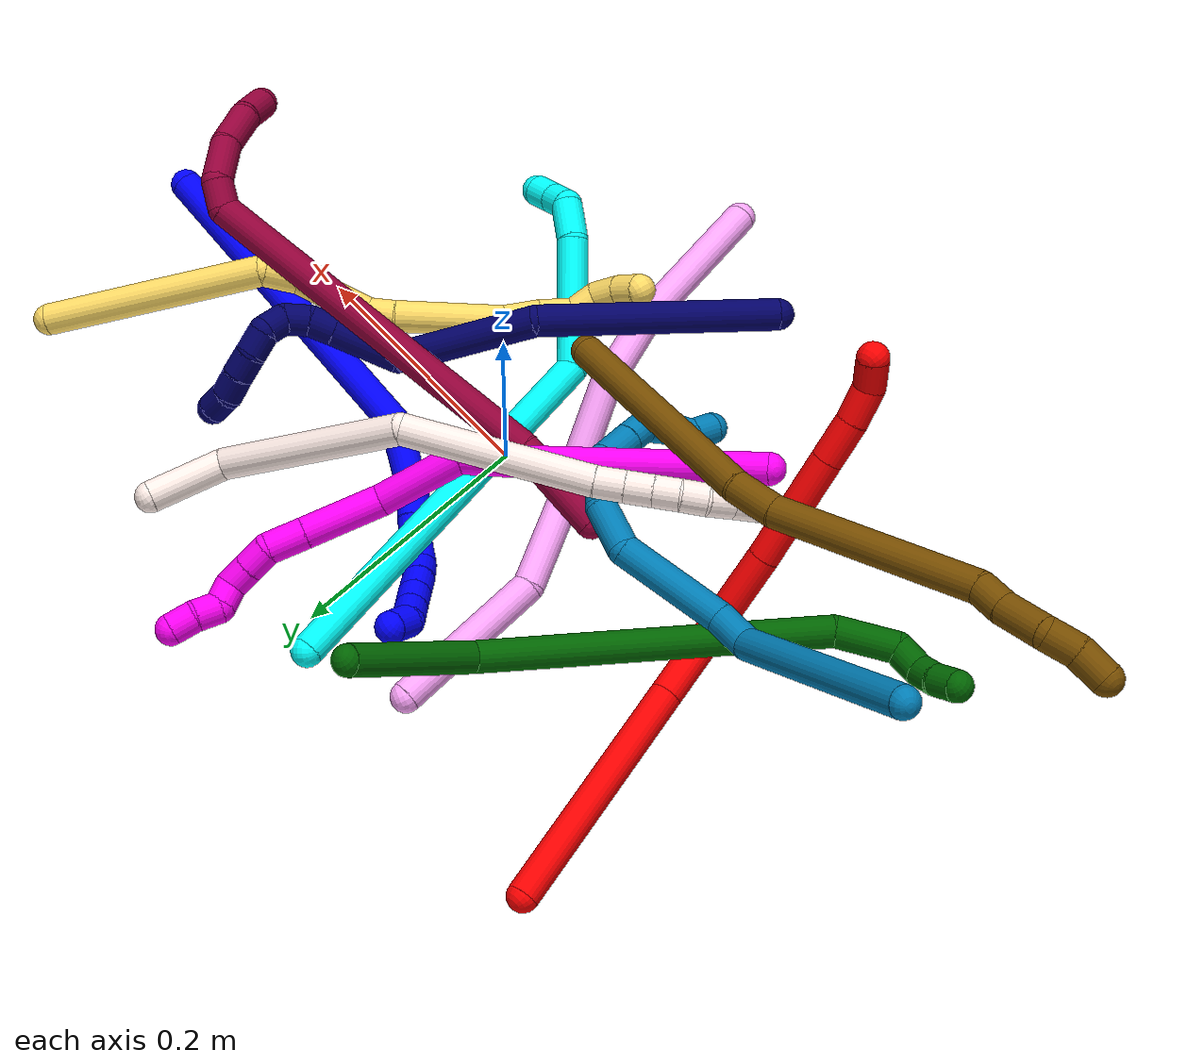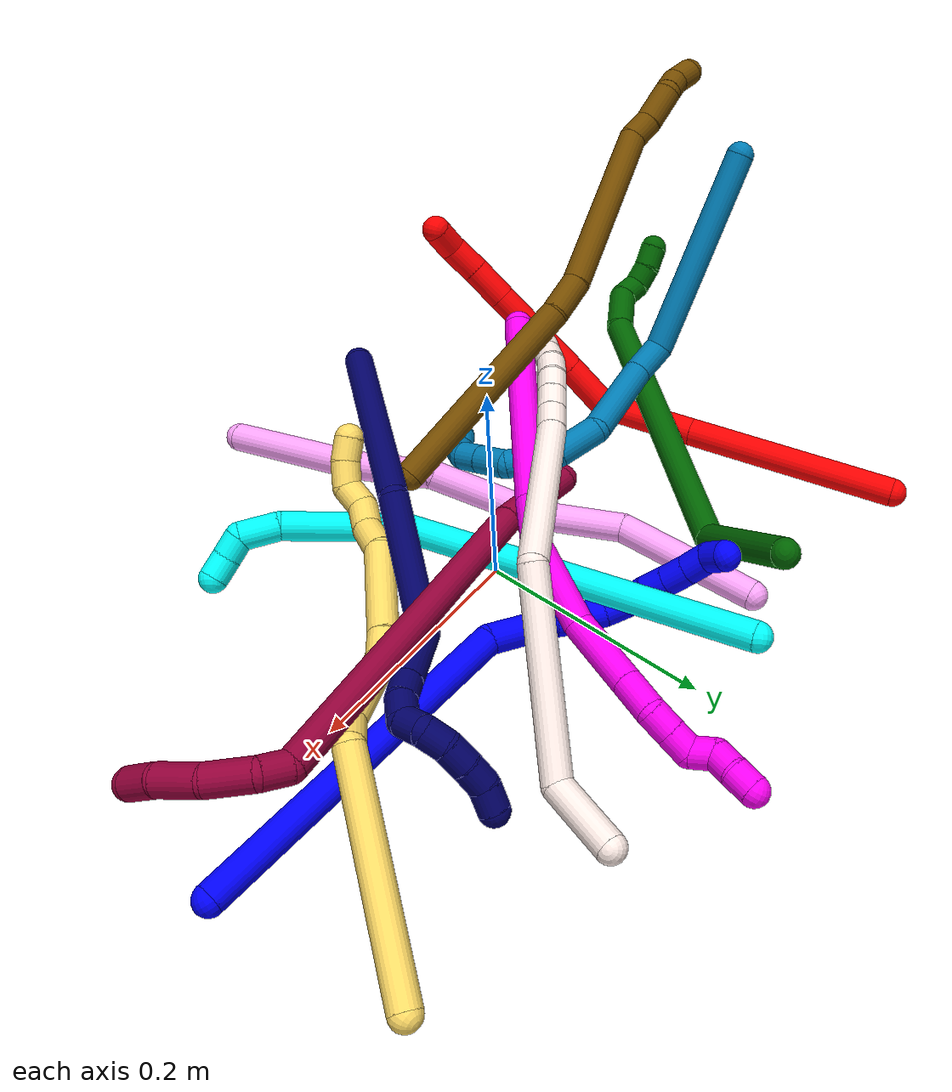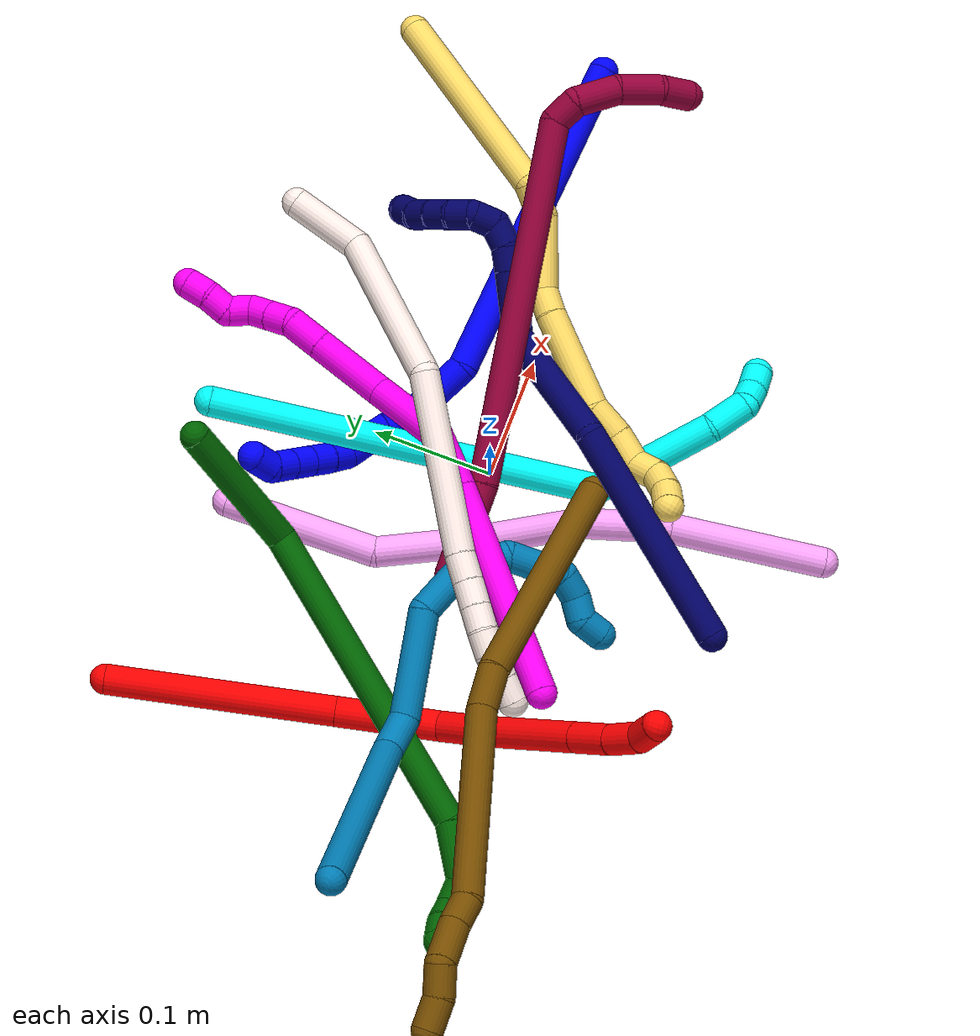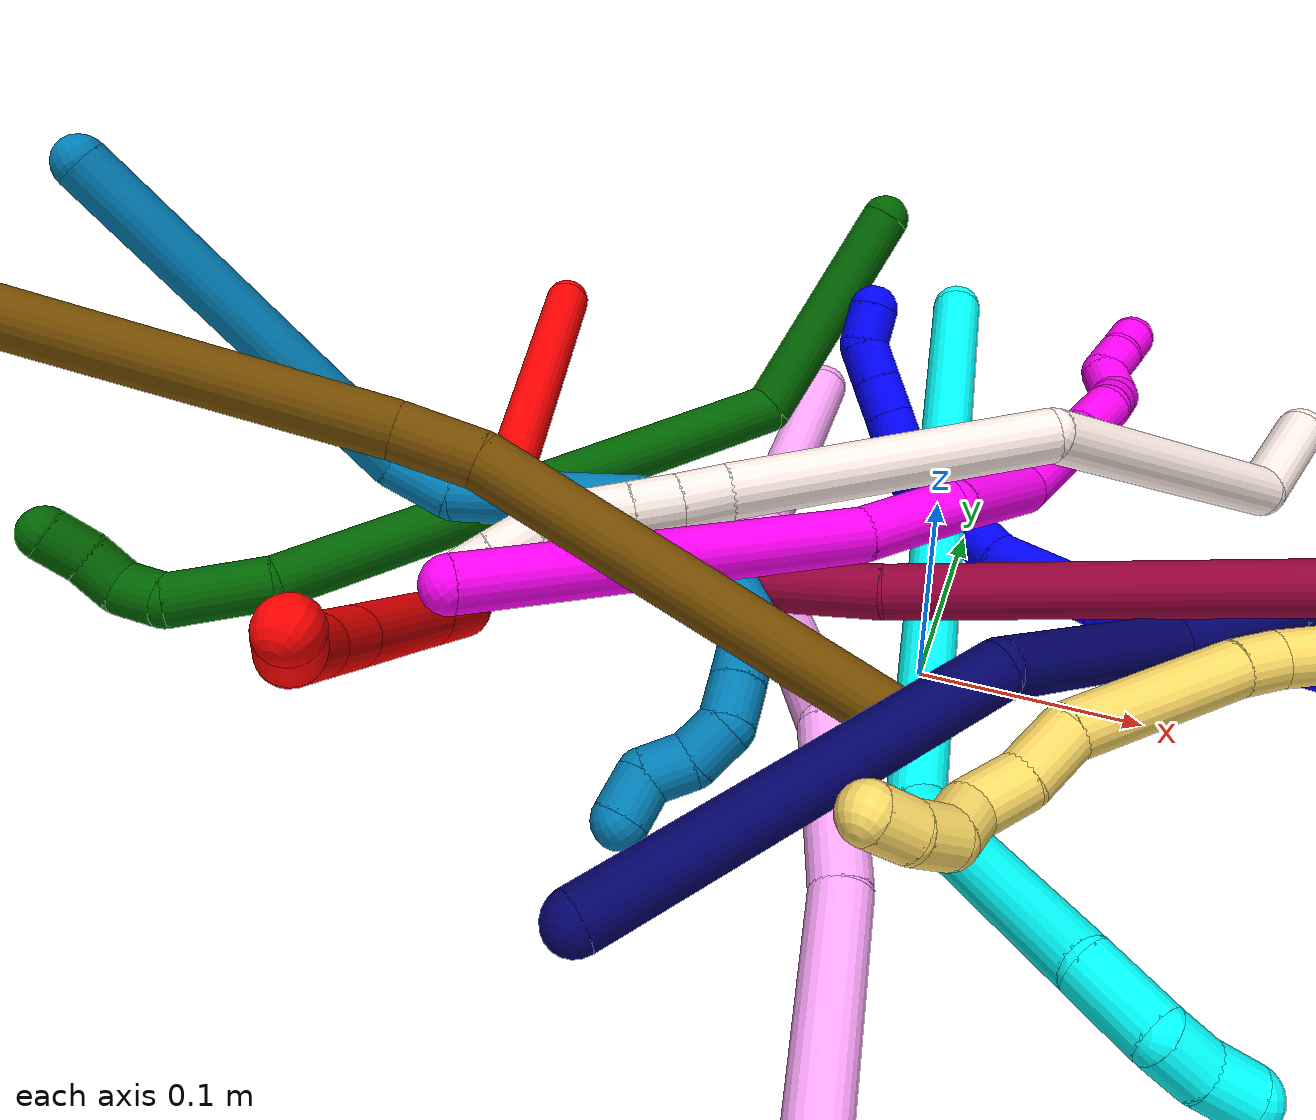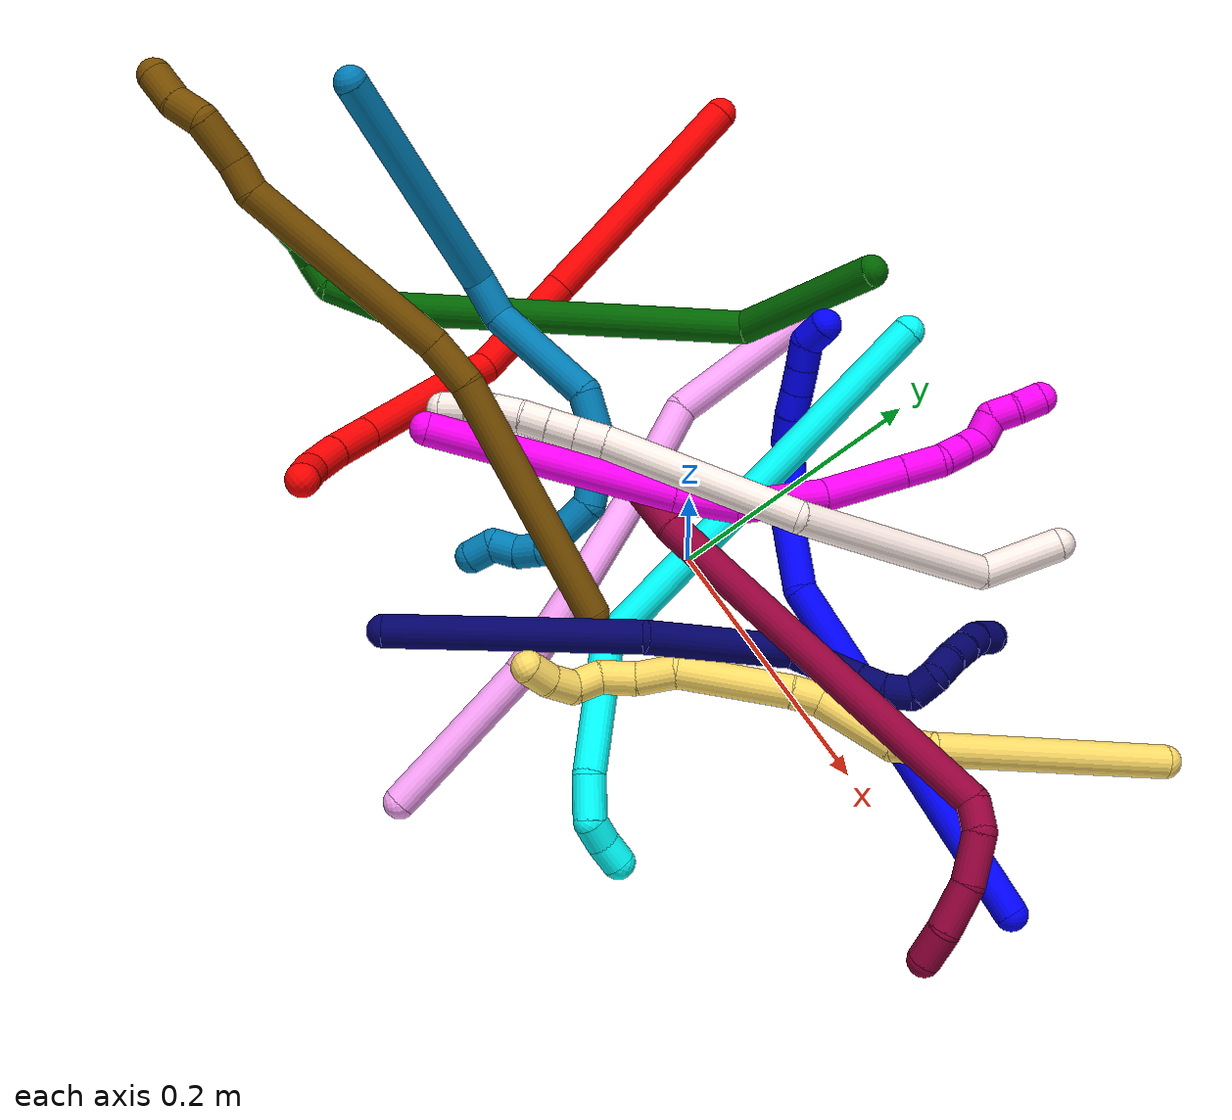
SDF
<sdf version="1.7">
 <world name="default">
  <plugin name="TubeGeneratorPlugin" filename="libtube_generator_plugin.so"/>
  <model name="photoneo_s_sensor">
   <static>1</static>
   <pose>0 0 2 1.57079 1.57079 3.14159</pose>
   <link name="link">
    <inertial><mass>0.1</mass></inertial>
    <sensor name="sensor" type="depth">
     <update_rate>30</update_rate>
     <camera>
      <horizontal_fov>1.22</horizontal_fov>
      <image><width>1920</width><height>1200</height><format>B8G8R8</format></image>
      <clip><near>0.1</near><far>4</far></clip>
      <depth_camera><output>points</output></depth_camera>
     </camera>
     <plugin name="camera_plugin" filename="libgazebo_ros_depth_camera.so">
      <baseline>0.2</baseline>
      <alwaysOn>1</alwaysOn>
      <updateRate>0.0</updateRate>
      <cameraName>camera_ir</cameraName>
      <imageTopicName>/camera/color/image_raw</imageTopicName>
      <cameraInfoTopicName>/camera/color/camera_info</cameraInfoTopicName>
      <depthImageTopicName>/camera/depth/image_raw</depthImageTopicName>
      <depthImageCameraInfoTopicName>/camera/depth/camera_info</depthImageCameraInfoTopicName>
      <pointCloudTopicName>/camera/depth/points</pointCloudTopicName>
      <frameName>fr_optical</frameName>
      <pointCloudCutoff>0.1</pointCloudCutoff>
      <pointCloudCutoffMax>2.0</pointCloudCutoffMax>
      <distortionK1>0</distortionK1>
      <distortionK2>0</distortionK2>
      <distortionK3>0</distortionK3>
      <distortionT1>0</distortionT1>
      <distortionT2>0</distortionT2>
      <CxPrime>0</CxPrime>
      <Cx>0</Cx>
      <Cy>0</Cy>
      <focalLength>0</focalLength>
      <hackBaseline>0</hackBaseline>
     </plugin>
    </sensor>
   </link>
  </model>
  <gravity>0 0 -9.8</gravity>
  <magnetic_field>6e-06 2.3e-05 -4.2e-05</magnetic_field>
  <atmosphere type="adiabatic"/>
  <physics name="default_physics" default="0" type="ode">
   <max_step_size>0.003</max_step_size>
   <real_time_factor>1</real_time_factor>
   <real_time_update_rate>1000</real_time_update_rate>
   <max_contacts>10000</max_contacts>
   <ode>
    <solver>
     <type>quick</type>
     <iters>100</iters>
     <sor>1.3</sor>
     <use_dynamic_moi_rescaling>0</use_dynamic_moi_rescaling>
    </solver>
    <constraints>
     <contact_max_correcting_vel>0</contact_max_correcting_vel>
     <contact_surface_layer>0.001</contact_surface_layer>
     <cfm>0</cfm>
     <erp>0.2</erp>
    </constraints>
   </ode>
  </physics>
  <scene><ambient>0.4 0.4 0.4 1</ambient><background>0.7 0.7 0.7 1</background><shadows>0</shadows></scene>
  <audio><device>default</device></audio>
  <spherical_coordinates>
   <surface_model>EARTH_WGS84</surface_model>
   <latitude_deg>0</latitude_deg>
   <longitude_deg>0</longitude_deg>
   <elevation>0</elevation>
   <heading_deg>0</heading_deg>
  </spherical_coordinates>
  <model name="bin">
   <static>1</static>
   <link name="bottom">
    <collision name="collision-bottom">
     <pose>0 0 -0.01 0 -0 0</pose>
     <geometry><box><size>0.8 0.6 0.02</size></box></geometry>
     <surface>
      <friction><ode><mu>100</mu><mu2>100</mu2></ode></friction>
      <contact><collide_bitmask>65535</collide_bitmask></contact>
     </surface>
    </collision>
   </link>
   <link name="west_wall">
    <collision name="collision-west_wall">
     <pose>-0.41 0 0.1 0 -0 0</pose>
     <geometry><box><size>0.02 0.6 0.2</size></box></geometry>
     <surface>
      <friction><ode><mu>100</mu><mu2>100</mu2></ode></friction>
      <contact><collide_bitmask>65535</collide_bitmask></contact>
     </surface>
    </collision>
   </link>
   <link name="east_wall">
    <collision name="collision-east_wall">
     <pose>0.41 0 0.1 0 -0 0</pose>
     <geometry><box><size>0.02 0.6 0.2</size></box></geometry>
     <surface>
      <friction><ode><mu>100</mu><mu2>100</mu2></ode></friction>
      <contact><collide_bitmask>65535</collide_bitmask></contact>
     </surface>
    </collision>
   </link>
   <link name="south_wall">
    <collision name="collision-south_wall">
     <pose>0 -0.31 0.1 0 -0 0</pose>
     <geometry><box><size>0.8 0.02 0.2</size></box></geometry>
     <surface>
      <friction><ode><mu>100</mu><mu2>100</mu2></ode></friction>
      <contact><collide_bitmask>65535</collide_bitmask></contact>
     </surface>
    </collision>
   </link>
   <link name="north_wall">
    <collision name="collision-north_wall">
     <pose>0 0.31 0.1 0 -0 0</pose>
     <geometry><box><size>0.8 0.02 0.2</size></box></geometry>
     <surface>
      <friction><ode><mu>100</mu><mu2>100</mu2></ode></friction>
      <contact><collide_bitmask>65535</collide_bitmask></contact>
     </surface>
    </collision>
   </link>
  </model>
  <model name="1">
   <static>0</static>
   <link name="1">
    <collision name="collision-cylinder-e_1_1_4">
     <pose>-0.137871 0.019291 0.017713 -0.828016 -1.38308 0.697822</pose>
     <geometry><cylinder><radius>0.0125</radius><length>0.280673</length></cylinder></geometry>
     <surface>
      <friction><ode><mu>1.16</mu><mu2>1.16</mu2><slip1>0</slip1><slip2>0</slip2></ode></friction>
      <contact><ode><kp>1e+06</kp><kd>1</kd><max_vel>0</max_vel><min_depth>0.001</min_depth></ode></contact>
     </surface>
    </collision>
    <visual name="visual-cylinder-e_1_1_4">
     <pose>-0.137871 0.019291 0.017713 -0.828016 -1.38308 0.697822</pose>
     <geometry><cylinder><radius>0.0125</radius><length>0.280673</length></cylinder></geometry>
     <material><ambient>0 0 1 1</ambient></material>
    </visual>
    <collision name="collision-cylinder-e_2_4_5">
     <pose>-0.302172 0.045808 0.026489 -2.46166 -1.16062 2.15212</pose>
     <geometry><cylinder><radius>0.0125</radius><length>0.057641</length></cylinder></geometry>
     <surface>
      <friction><ode><mu>1.16</mu><mu2>1.16</mu2><slip1>0</slip1><slip2>0</slip2></ode></friction>
      <contact><ode><kp>1e+06</kp><kd>1</kd><max_vel>0</max_vel><min_depth>0.001</min_depth></ode></contact>
     </surface>
    </collision>
    <visual name="visual-cylinder-e_2_4_5">
     <pose>-0.302172 0.045808 0.026489 -2.46166 -1.16062 2.15212</pose>
     <geometry><cylinder><radius>0.0125</radius><length>0.057641</length></cylinder></geometry>
     <material><ambient>0 0 1 1</ambient></material>
    </visual>
    <collision name="collision-cylinder-e_3_5_6">
     <pose>-0.336591 0.058175 0.013729 -2.21019 -0.894847 1.52462</pose>
     <geometry><cylinder><radius>0.0125</radius><length>0.020479</length></cylinder></geometry>
     <surface>
      <friction><ode><mu>1.16</mu><mu2>1.16</mu2><slip1>0</slip1><slip2>0</slip2></ode></friction>
      <contact><ode><kp>1e+06</kp><kd>1</kd><max_vel>0</max_vel><min_depth>0.001</min_depth></ode></contact>
     </surface>
    </collision>
    <visual name="visual-cylinder-e_3_5_6">
     <pose>-0.336591 0.058175 0.013729 -2.21019 -0.894847 1.52462</pose>
     <geometry><cylinder><radius>0.0125</radius><length>0.020479</length></cylinder></geometry>
     <material><ambient>0 0 1 1</ambient></material>
    </visual>
    <collision name="collision-cylinder-e_4_6_7">
     <pose>-0.353356 0.067948 0.006666 -2.18118 -0.998525 1.61669</pose>
     <geometry><cylinder><radius>0.0125</radius><length>0.020881</length></cylinder></geometry>
     <surface>
      <friction><ode><mu>1.16</mu><mu2>1.16</mu2><slip1>0</slip1><slip2>0</slip2></ode></friction>
      <contact><ode><kp>1e+06</kp><kd>1</kd><max_vel>0</max_vel><min_depth>0.001</min_depth></ode></contact>
     </surface>
    </collision>
    <visual name="visual-cylinder-e_4_6_7">
     <pose>-0.353356 0.067948 0.006666 -2.18118 -0.998525 1.61669</pose>
     <geometry><cylinder><radius>0.0125</radius><length>0.020881</length></cylinder></geometry>
     <material><ambient>0 0 1 1</ambient></material>
    </visual>
    <collision name="collision-cylinder-e_5_7_8">
     <pose>-0.370454 0.077964 0.001933 -1.84121 -0.979668 1.2229</pose>
     <geometry><cylinder><radius>0.0125</radius><length>0.020045</length></cylinder></geometry>
     <surface>
      <friction><ode><mu>1.16</mu><mu2>1.16</mu2><slip1>0</slip1><slip2>0</slip2></ode></friction>
      <contact><ode><kp>1e+06</kp><kd>1</kd><max_vel>0</max_vel><min_depth>0.001</min_depth></ode></contact>
     </surface>
    </collision>
    <visual name="visual-cylinder-e_5_7_8">
     <pose>-0.370454 0.077964 0.001933 -1.84121 -0.979668 1.2229</pose>
     <geometry><cylinder><radius>0.0125</radius><length>0.020045</length></cylinder></geometry>
     <material><ambient>0 0 1 1</ambient></material>
    </visual>
    <collision name="collision-cylinder-e_6_8_9">
     <pose>-0.383831 0.092052 0.001213 -1.48228 -0.524315 0.481616</pose>
     <geometry><cylinder><radius>0.0125</radius><length>0.020192</length></cylinder></geometry>
     <surface>
      <friction><ode><mu>1.16</mu><mu2>1.16</mu2><slip1>0</slip1><slip2>0</slip2></ode></friction>
      <contact><ode><kp>1e+06</kp><kd>1</kd><max_vel>0</max_vel><min_depth>0.001</min_depth></ode></contact>
     </surface>
    </collision>
    <visual name="visual-cylinder-e_6_8_9">
     <pose>-0.383831 0.092052 0.001213 -1.48228 -0.524315 0.481616</pose>
     <geometry><cylinder><radius>0.0125</radius><length>0.020192</length></cylinder></geometry>
     <material><ambient>0 0 1 1</ambient></material>
    </visual>
    <collision name="collision-cylinder-e_7_9_10">
     <pose>-0.393488 0.109648 0.002005 -1.56868 -0.477736 0.476765</pose>
     <geometry><cylinder><radius>0.0125</radius><length>0.020023</length></cylinder></geometry>
     <surface>
      <friction><ode><mu>1.16</mu><mu2>1.16</mu2><slip1>0</slip1><slip2>0</slip2></ode></friction>
      <contact><ode><kp>1e+06</kp><kd>1</kd><max_vel>0</max_vel><min_depth>0.001</min_depth></ode></contact>
     </surface>
    </collision>
    <visual name="visual-cylinder-e_7_9_10">
     <pose>-0.393488 0.109648 0.002005 -1.56868 -0.477736 0.476765</pose>
     <geometry><cylinder><radius>0.0125</radius><length>0.020023</length></cylinder></geometry>
     <material><ambient>0 0 1 1</ambient></material>
    </visual>
    <collision name="collision-cylinder-e_8_10_11">
     <pose>-0.402715 0.127424 0.002408 -1.52756 -0.47942 0.45985</pose>
     <geometry><cylinder><radius>0.0125</radius><length>0.020048</length></cylinder></geometry>
     <surface>
      <friction><ode><mu>1.16</mu><mu2>1.16</mu2><slip1>0</slip1><slip2>0</slip2></ode></friction>
      <contact><ode><kp>1e+06</kp><kd>1</kd><max_vel>0</max_vel><min_depth>0.001</min_depth></ode></contact>
     </surface>
    </collision>
    <visual name="visual-cylinder-e_8_10_11">
     <pose>-0.402715 0.127424 0.002408 -1.52756 -0.47942 0.45985</pose>
     <geometry><cylinder><radius>0.0125</radius><length>0.020048</length></cylinder></geometry>
     <material><ambient>0 0 1 1</ambient></material>
    </visual>
    <collision name="collision-cylinder-e_9_11_12">
     <pose>-0.411768 0.145226 0.003741 -1.46478 -0.458835 0.413978</pose>
     <geometry><cylinder><radius>0.0125</radius><length>0.020003</length></cylinder></geometry>
     <surface>
      <friction><ode><mu>1.16</mu><mu2>1.16</mu2><slip1>0</slip1><slip2>0</slip2></ode></friction>
      <contact><ode><kp>1e+06</kp><kd>1</kd><max_vel>0</max_vel><min_depth>0.001</min_depth></ode></contact>
     </surface>
    </collision>
    <visual name="visual-cylinder-e_9_11_12">
     <pose>-0.411768 0.145226 0.003741 -1.46478 -0.458835 0.413978</pose>
     <geometry><cylinder><radius>0.0125</radius><length>0.020003</length></cylinder></geometry>
     <material><ambient>0 0 1 1</ambient></material>
    </visual>
    <collision name="collision-cylinder-e_10_12_2">
     <pose>-0.415349 0.164022 0.003335 -1.70711 0.084923 -0.097348</pose>
     <geometry><cylinder><radius>0.0125</radius><length>0.020014</length></cylinder></geometry>
     <surface>
      <friction><ode><mu>1.16</mu><mu2>1.16</mu2><slip1>0</slip1><slip2>0</slip2></ode></friction>
      <contact><ode><kp>1e+06</kp><kd>1</kd><max_vel>0</max_vel><min_depth>0.001</min_depth></ode></contact>
     </surface>
    </collision>
    <visual name="visual-cylinder-e_10_12_2">
     <pose>-0.415349 0.164022 0.003335 -1.70711 0.084923 -0.097348</pose>
     <geometry><cylinder><radius>0.0125</radius><length>0.020014</length></cylinder></geometry>
     <material><ambient>0 0 1 1</ambient></material>
    </visual>
    <collision name="collision-sphere-2">
     <pose>-0.4145 0.1739 0.00198 0 -0 0</pose>
     <geometry><sphere><radius>0.0125</radius></sphere></geometry>
     <surface>
      <friction><ode><mu>1.16</mu><mu2>1.16</mu2><slip1>0</slip1><slip2>0</slip2></ode></friction>
      <contact><ode><kp>1e+06</kp><kd>1</kd><max_vel>0</max_vel><min_depth>0.001</min_depth></ode></contact>
     </surface>
    </collision>
    <visual name="visual-sphere-2">
     <pose>-0.4145 0.1739 0.00198 0 -0 0</pose>
     <geometry><sphere><radius>0.0125</radius></sphere></geometry>
     <material><ambient>0 0 1 1</ambient></material>
    </visual>
    <collision name="collision-sphere-12">
     <pose>-0.416198 0.154143 0.00469 0 -0 0</pose>
     <geometry><sphere><radius>0.0125</radius></sphere></geometry>
     <surface>
      <friction><ode><mu>1.16</mu><mu2>1.16</mu2><slip1>0</slip1><slip2>0</slip2></ode></friction>
      <contact><ode><kp>1e+06</kp><kd>1</kd><max_vel>0</max_vel><min_depth>0.001</min_depth></ode></contact>
     </surface>
    </collision>
    <visual name="visual-sphere-12">
     <pose>-0.416198 0.154143 0.00469 0 -0 0</pose>
     <geometry><sphere><radius>0.0125</radius></sphere></geometry>
     <material><ambient>0 0 1 1</ambient></material>
    </visual>
    <collision name="collision-sphere-11">
     <pose>-0.407338 0.13631 0.002792 0 -0 0</pose>
     <geometry><sphere><radius>0.0125</radius></sphere></geometry>
     <surface>
      <friction><ode><mu>1.16</mu><mu2>1.16</mu2><slip1>0</slip1><slip2>0</slip2></ode></friction>
      <contact><ode><kp>1e+06</kp><kd>1</kd><max_vel>0</max_vel><min_depth>0.001</min_depth></ode></contact>
     </surface>
    </collision>
    <visual name="visual-sphere-11">
     <pose>-0.407338 0.13631 0.002792 0 -0 0</pose>
     <geometry><sphere><radius>0.0125</radius></sphere></geometry>
     <material><ambient>0 0 1 1</ambient></material>
    </visual>
    <collision name="collision-sphere-10">
     <pose>-0.398091 0.118539 0.002024 0 -0 0</pose>
     <geometry><sphere><radius>0.0125</radius></sphere></geometry>
     <surface>
      <friction><ode><mu>1.16</mu><mu2>1.16</mu2><slip1>0</slip1><slip2>0</slip2></ode></friction>
      <contact><ode><kp>1e+06</kp><kd>1</kd><max_vel>0</max_vel><min_depth>0.001</min_depth></ode></contact>
     </surface>
    </collision>
    <visual name="visual-sphere-10">
     <pose>-0.398091 0.118539 0.002024 0 -0 0</pose>
     <geometry><sphere><radius>0.0125</radius></sphere></geometry>
     <material><ambient>0 0 1 1</ambient></material>
    </visual>
    <collision name="collision-sphere-9">
     <pose>-0.388885 0.100758 0.001986 0 -0 0</pose>
     <geometry><sphere><radius>0.0125</radius></sphere></geometry>
     <surface>
      <friction><ode><mu>1.16</mu><mu2>1.16</mu2><slip1>0</slip1><slip2>0</slip2></ode></friction>
      <contact><ode><kp>1e+06</kp><kd>1</kd><max_vel>0</max_vel><min_depth>0.001</min_depth></ode></contact>
     </surface>
    </collision>
    <visual name="visual-sphere-9">
     <pose>-0.388885 0.100758 0.001986 0 -0 0</pose>
     <geometry><sphere><radius>0.0125</radius></sphere></geometry>
     <material><ambient>0 0 1 1</ambient></material>
    </visual>
    <collision name="collision-sphere-4">
     <pose>-0.275742 0.038582 0.035426 0 -0 0</pose>
     <geometry><sphere><radius>0.0125</radius></sphere></geometry>
     <surface>
      <friction><ode><mu>1.16</mu><mu2>1.16</mu2><slip1>0</slip1><slip2>0</slip2></ode></friction>
      <contact><ode><kp>1e+06</kp><kd>1</kd><max_vel>0</max_vel><min_depth>0.001</min_depth></ode></contact>
     </surface>
    </collision>
    <visual name="visual-sphere-4">
     <pose>-0.275742 0.038582 0.035426 0 -0 0</pose>
     <geometry><sphere><radius>0.0125</radius></sphere></geometry>
     <material><ambient>0 0 1 1</ambient></material>
    </visual>
    <collision name="collision-sphere-1">
     <geometry><sphere><radius>0.0125</radius></sphere></geometry>
     <surface>
      <friction><ode><mu>1.16</mu><mu2>1.16</mu2><slip1>0</slip1><slip2>0</slip2></ode></friction>
      <contact><ode><kp>1e+06</kp><kd>1</kd><max_vel>0</max_vel><min_depth>0.001</min_depth></ode></contact>
     </surface>
    </collision>
    <visual name="visual-sphere-1">
     <geometry><sphere><radius>0.0125</radius></sphere></geometry>
     <material><ambient>0 0 1 1</ambient></material>
    </visual>
    <collision name="collision-sphere-8">
     <pose>-0.378776 0.083347 0.000441 0 -0 0</pose>
     <geometry><sphere><radius>0.0125</radius></sphere></geometry>
     <surface>
      <friction><ode><mu>1.16</mu><mu2>1.16</mu2><slip1>0</slip1><slip2>0</slip2></ode></friction>
      <contact><ode><kp>1e+06</kp><kd>1</kd><max_vel>0</max_vel><min_depth>0.001</min_depth></ode></contact>
     </surface>
    </collision>
    <visual name="visual-sphere-8">
     <pose>-0.378776 0.083347 0.000441 0 -0 0</pose>
     <geometry><sphere><radius>0.0125</radius></sphere></geometry>
     <material><ambient>0 0 1 1</ambient></material>
    </visual>
    <collision name="collision-sphere-5">
     <pose>-0.328602 0.053034 0.017552 0 -0 0</pose>
     <geometry><sphere><radius>0.0125</radius></sphere></geometry>
     <surface>
      <friction><ode><mu>1.16</mu><mu2>1.16</mu2><slip1>0</slip1><slip2>0</slip2></ode></friction>
      <contact><ode><kp>1e+06</kp><kd>1</kd><max_vel>0</max_vel><min_depth>0.001</min_depth></ode></contact>
     </surface>
    </collision>
    <visual name="visual-sphere-5">
     <pose>-0.328602 0.053034 0.017552 0 -0 0</pose>
     <geometry><sphere><radius>0.0125</radius></sphere></geometry>
     <material><ambient>0 0 1 1</ambient></material>
    </visual>
    <collision name="collision-sphere-6">
     <pose>-0.344579 0.063315 0.009906 0 -0 0</pose>
     <geometry><sphere><radius>0.0125</radius></sphere></geometry>
     <surface>
      <friction><ode><mu>1.16</mu><mu2>1.16</mu2><slip1>0</slip1><slip2>0</slip2></ode></friction>
      <contact><ode><kp>1e+06</kp><kd>1</kd><max_vel>0</max_vel><min_depth>0.001</min_depth></ode></contact>
     </surface>
    </collision>
    <visual name="visual-sphere-6">
     <pose>-0.344579 0.063315 0.009906 0 -0 0</pose>
     <geometry><sphere><radius>0.0125</radius></sphere></geometry>
     <material><ambient>0 0 1 1</ambient></material>
    </visual>
    <collision name="collision-sphere-7">
     <pose>-0.362133 0.072581 0.003425 0 -0 0</pose>
     <geometry><sphere><radius>0.0125</radius></sphere></geometry>
     <surface>
      <friction><ode><mu>1.16</mu><mu2>1.16</mu2><slip1>0</slip1><slip2>0</slip2></ode></friction>
      <contact><ode><kp>1e+06</kp><kd>1</kd><max_vel>0</max_vel><min_depth>0.001</min_depth></ode></contact>
     </surface>
    </collision>
    <visual name="visual-sphere-7">
     <pose>-0.362133 0.072581 0.003425 0 -0 0</pose>
     <geometry><sphere><radius>0.0125</radius></sphere></geometry>
     <material><ambient>0 0 1 1</ambient></material>
    </visual>
    <inertial>
     <pose>-0.236128 0.050049 0.014424 0 -0 0</pose>
     <mass>0.5</mass>
     <inertia>
      <ixx>0.000468</ixx>
      <ixy>0</ixy>
      <ixz>0</ixz>
      <iyy>0.00209</iyy>
      <iyz>0</iyz>
      <izz>0.001576</izz>
     </inertia>
    </inertial>
   </link>
   <pose>0.351186 0.033736 0.011631 0.845478 -0.155348 -0.064842</pose>
  </model>
  <model name="2">
   <static>0</static>
   <link name="2">
    <collision name="collision-cylinder-e_1_1_4">
     <pose>0.01626 -0.006768 -0.091686 3.06791 0.175052 2.34627</pose>
     <geometry><cylinder><radius>0.0125</radius><length>0.186725</length></cylinder></geometry>
     <surface>
      <friction><ode><mu>1.16</mu><mu2>1.16</mu2><slip1>0</slip1><slip2>0</slip2></ode></friction>
      <contact><ode><kp>1e+06</kp><kd>1</kd><max_vel>0</max_vel><min_depth>0.001</min_depth></ode></contact>
     </surface>
    </collision>
    <visual name="visual-cylinder-e_1_1_4">
     <pose>0.01626 -0.006768 -0.091686 3.06791 0.175052 2.34627</pose>
     <geometry><cylinder><radius>0.0125</radius><length>0.186725</length></cylinder></geometry>
     <material><ambient>1 0 0 1</ambient></material>
    </visual>
    <collision name="collision-cylinder-e_2_4_5">
     <pose>0.039907 -0.016698 -0.225477 3.06665 0.173208 2.32635</pose>
     <geometry><cylinder><radius>0.0125</radius><length>0.08573</length></cylinder></geometry>
     <surface>
      <friction><ode><mu>1.16</mu><mu2>1.16</mu2><slip1>0</slip1><slip2>0</slip2></ode></friction>
      <contact><ode><kp>1e+06</kp><kd>1</kd><max_vel>0</max_vel><min_depth>0.001</min_depth></ode></contact>
     </surface>
    </collision>
    <visual name="visual-cylinder-e_2_4_5">
     <pose>0.039907 -0.016698 -0.225477 3.06665 0.173208 2.32635</pose>
     <geometry><cylinder><radius>0.0125</radius><length>0.08573</length></cylinder></geometry>
     <material><ambient>1 0 0 1</ambient></material>
    </visual>
    <collision name="collision-cylinder-e_3_5_6">
     <pose>0.052917 -0.03618 -0.284648 2.37848 0.233735 0.56934</pose>
     <geometry><cylinder><radius>0.0125</radius><length>0.048547</length></cylinder></geometry>
     <surface>
      <friction><ode><mu>1.16</mu><mu2>1.16</mu2><slip1>0</slip1><slip2>0</slip2></ode></friction>
      <contact><ode><kp>1e+06</kp><kd>1</kd><max_vel>0</max_vel><min_depth>0.001</min_depth></ode></contact>
     </surface>
    </collision>
    <visual name="visual-cylinder-e_3_5_6">
     <pose>0.052917 -0.03618 -0.284648 2.37848 0.233735 0.56934</pose>
     <geometry><cylinder><radius>0.0125</radius><length>0.048547</length></cylinder></geometry>
     <material><ambient>1 0 0 1</ambient></material>
    </visual>
    <collision name="collision-cylinder-e_4_6_7">
     <pose>0.070531 -0.082741 -0.333146 2.37552 0.268318 0.646439</pose>
     <geometry><cylinder><radius>0.0125</radius><length>0.090472</length></cylinder></geometry>
     <surface>
      <friction><ode><mu>1.16</mu><mu2>1.16</mu2><slip1>0</slip1><slip2>0</slip2></ode></friction>
      <contact><ode><kp>1e+06</kp><kd>1</kd><max_vel>0</max_vel><min_depth>0.001</min_depth></ode></contact>
     </surface>
    </collision>
    <visual name="visual-cylinder-e_4_6_7">
     <pose>0.070531 -0.082741 -0.333146 2.37552 0.268318 0.646439</pose>
     <geometry><cylinder><radius>0.0125</radius><length>0.090472</length></cylinder></geometry>
     <material><ambient>1 0 0 1</ambient></material>
    </visual>
    <collision name="collision-cylinder-e_5_7_8">
     <pose>0.087124 -0.124623 -0.376558 2.3705 0.268718 0.643004</pose>
     <geometry><cylinder><radius>0.0125</radius><length>0.034652</length></cylinder></geometry>
     <surface>
      <friction><ode><mu>1.16</mu><mu2>1.16</mu2><slip1>0</slip1><slip2>0</slip2></ode></friction>
      <contact><ode><kp>1e+06</kp><kd>1</kd><max_vel>0</max_vel><min_depth>0.001</min_depth></ode></contact>
     </surface>
    </collision>
    <visual name="visual-cylinder-e_5_7_8">
     <pose>0.087124 -0.124623 -0.376558 2.3705 0.268718 0.643004</pose>
     <geometry><cylinder><radius>0.0125</radius><length>0.034652</length></cylinder></geometry>
     <material><ambient>1 0 0 1</ambient></material>
    </visual>
    <collision name="collision-cylinder-e_6_8_9">
     <pose>0.097031 -0.145882 -0.39799 2.34756 0.374961 0.849797</pose>
     <geometry><cylinder><radius>0.0125</radius><length>0.028984</length></cylinder></geometry>
     <surface>
      <friction><ode><mu>1.16</mu><mu2>1.16</mu2><slip1>0</slip1><slip2>0</slip2></ode></friction>
      <contact><ode><kp>1e+06</kp><kd>1</kd><max_vel>0</max_vel><min_depth>0.001</min_depth></ode></contact>
     </surface>
    </collision>
    <visual name="visual-cylinder-e_6_8_9">
     <pose>0.097031 -0.145882 -0.39799 2.34756 0.374961 0.849797</pose>
     <geometry><cylinder><radius>0.0125</radius><length>0.028984</length></cylinder></geometry>
     <material><ambient>1 0 0 1</ambient></material>
    </visual>
    <collision name="collision-cylinder-e_7_9_2">
     <pose>0.109513 -0.165003 -0.411062 1.9347 0.61435 0.862707</pose>
     <geometry><cylinder><radius>0.0125</radius><length>0.02489</length></cylinder></geometry>
     <surface>
      <friction><ode><mu>1.16</mu><mu2>1.16</mu2><slip1>0</slip1><slip2>0</slip2></ode></friction>
      <contact><ode><kp>1e+06</kp><kd>1</kd><max_vel>0</max_vel><min_depth>0.001</min_depth></ode></contact>
     </surface>
    </collision>
    <visual name="visual-cylinder-e_7_9_2">
     <pose>0.109513 -0.165003 -0.411062 1.9347 0.61435 0.862707</pose>
     <geometry><cylinder><radius>0.0125</radius><length>0.02489</length></cylinder></geometry>
     <material><ambient>1 0 0 1</ambient></material>
    </visual>
    <collision name="collision-sphere-2">
     <pose>0.116686 -0.174506 -0.414681 0 -0 0</pose>
     <geometry><sphere><radius>0.0125</radius></sphere></geometry>
     <surface>
      <friction><ode><mu>1.16</mu><mu2>1.16</mu2><slip1>0</slip1><slip2>0</slip2></ode></friction>
      <contact><ode><kp>1e+06</kp><kd>1</kd><max_vel>0</max_vel><min_depth>0.001</min_depth></ode></contact>
     </surface>
    </collision>
    <visual name="visual-sphere-2">
     <pose>0.116686 -0.174506 -0.414681 0 -0 0</pose>
     <geometry><sphere><radius>0.0125</radius></sphere></geometry>
     <material><ambient>1 0 0 1</ambient></material>
    </visual>
    <collision name="collision-sphere-9">
     <pose>0.102339 -0.155499 -0.407442 0 -0 0</pose>
     <geometry><sphere><radius>0.0125</radius></sphere></geometry>
     <surface>
      <friction><ode><mu>1.16</mu><mu2>1.16</mu2><slip1>0</slip1><slip2>0</slip2></ode></friction>
      <contact><ode><kp>1e+06</kp><kd>1</kd><max_vel>0</max_vel><min_depth>0.001</min_depth></ode></contact>
     </surface>
    </collision>
    <visual name="visual-sphere-9">
     <pose>0.102339 -0.155499 -0.407442 0 -0 0</pose>
     <geometry><sphere><radius>0.0125</radius></sphere></geometry>
     <material><ambient>1 0 0 1</ambient></material>
    </visual>
    <collision name="collision-sphere-4">
     <pose>0.03252 -0.013536 -0.183372 0 -0 0</pose>
     <geometry><sphere><radius>0.0125</radius></sphere></geometry>
     <surface>
      <friction><ode><mu>1.16</mu><mu2>1.16</mu2><slip1>0</slip1><slip2>0</slip2></ode></friction>
      <contact><ode><kp>1e+06</kp><kd>1</kd><max_vel>0</max_vel><min_depth>0.001</min_depth></ode></contact>
     </surface>
    </collision>
    <visual name="visual-sphere-4">
     <pose>0.03252 -0.013536 -0.183372 0 -0 0</pose>
     <geometry><sphere><radius>0.0125</radius></sphere></geometry>
     <material><ambient>1 0 0 1</ambient></material>
    </visual>
    <collision name="collision-sphere-1">
     <geometry><sphere><radius>0.0125</radius></sphere></geometry>
     <surface>
      <friction><ode><mu>1.16</mu><mu2>1.16</mu2><slip1>0</slip1><slip2>0</slip2></ode></friction>
      <contact><ode><kp>1e+06</kp><kd>1</kd><max_vel>0</max_vel><min_depth>0.001</min_depth></ode></contact>
     </surface>
    </collision>
    <visual name="visual-sphere-1">
     <geometry><sphere><radius>0.0125</radius></sphere></geometry>
     <material><ambient>1 0 0 1</ambient></material>
    </visual>
    <collision name="collision-sphere-8">
     <pose>0.091724 -0.136265 -0.388537 0 -0 0</pose>
     <geometry><sphere><radius>0.0125</radius></sphere></geometry>
     <surface>
      <friction><ode><mu>1.16</mu><mu2>1.16</mu2><slip1>0</slip1><slip2>0</slip2></ode></friction>
      <contact><ode><kp>1e+06</kp><kd>1</kd><max_vel>0</max_vel><min_depth>0.001</min_depth></ode></contact>
     </surface>
    </collision>
    <visual name="visual-sphere-8">
     <pose>0.091724 -0.136265 -0.388537 0 -0 0</pose>
     <geometry><sphere><radius>0.0125</radius></sphere></geometry>
     <material><ambient>1 0 0 1</ambient></material>
    </visual>
    <collision name="collision-sphere-5">
     <pose>0.047295 -0.019859 -0.267583 0 -0 0</pose>
     <geometry><sphere><radius>0.0125</radius></sphere></geometry>
     <surface>
      <friction><ode><mu>1.16</mu><mu2>1.16</mu2><slip1>0</slip1><slip2>0</slip2></ode></friction>
      <contact><ode><kp>1e+06</kp><kd>1</kd><max_vel>0</max_vel><min_depth>0.001</min_depth></ode></contact>
     </surface>
    </collision>
    <visual name="visual-sphere-5">
     <pose>0.047295 -0.019859 -0.267583 0 -0 0</pose>
     <geometry><sphere><radius>0.0125</radius></sphere></geometry>
     <material><ambient>1 0 0 1</ambient></material>
    </visual>
    <collision name="collision-sphere-6">
     <pose>0.058539 -0.052501 -0.301713 0 -0 0</pose>
     <geometry><sphere><radius>0.0125</radius></sphere></geometry>
     <surface>
      <friction><ode><mu>1.16</mu><mu2>1.16</mu2><slip1>0</slip1><slip2>0</slip2></ode></friction>
      <contact><ode><kp>1e+06</kp><kd>1</kd><max_vel>0</max_vel><min_depth>0.001</min_depth></ode></contact>
     </surface>
    </collision>
    <visual name="visual-sphere-6">
     <pose>0.058539 -0.052501 -0.301713 0 -0 0</pose>
     <geometry><sphere><radius>0.0125</radius></sphere></geometry>
     <material><ambient>1 0 0 1</ambient></material>
    </visual>
    <collision name="collision-sphere-7">
     <pose>0.082524 -0.112982 -0.364578 0 -0 0</pose>
     <geometry><sphere><radius>0.0125</radius></sphere></geometry>
     <surface>
      <friction><ode><mu>1.16</mu><mu2>1.16</mu2><slip1>0</slip1><slip2>0</slip2></ode></friction>
      <contact><ode><kp>1e+06</kp><kd>1</kd><max_vel>0</max_vel><min_depth>0.001</min_depth></ode></contact>
     </surface>
    </collision>
    <visual name="visual-sphere-7">
     <pose>0.082524 -0.112982 -0.364578 0 -0 0</pose>
     <geometry><sphere><radius>0.0125</radius></sphere></geometry>
     <material><ambient>1 0 0 1</ambient></material>
    </visual>
    <inertial>
     <pose>0.047929 -0.049182 -0.230449 0 -0 0</pose>
     <mass>0.5</mass>
     <inertia>
      <ixx>0.000136</ixx>
      <ixy>0</ixy>
      <ixz>0</ixz>
      <iyy>0.000852</iyy>
      <iyz>0</iyz>
      <izz>-5.9e-05</izz>
     </inertia>
    </inertial>
   </link>
   <pose>-0.270247 0.227419 0.012813 -1.4391 -0.289207 0.040426</pose>
  </model>
  <model name="3">
   <static>0</static>
   <link name="3">
    <collision name="collision-cylinder-e_1_1_4">
     <pose>0.051969 -0.143662 0.049265 1.24044 0.329693 0.236528</pose>
     <geometry><cylinder><radius>0.0125</radius><length>0.321039</length></cylinder></geometry>
     <surface>
      <friction><ode><mu>1.16</mu><mu2>1.16</mu2><slip1>0</slip1><slip2>0</slip2></ode></friction>
      <contact><ode><kp>1e+06</kp><kd>1</kd><max_vel>0</max_vel><min_depth>0.001</min_depth></ode></contact>
     </surface>
    </collision>
    <visual name="visual-cylinder-e_1_1_4">
     <pose>0.051969 -0.143662 0.049265 1.24044 0.329693 0.236528</pose>
     <geometry><cylinder><radius>0.0125</radius><length>0.321039</length></cylinder></geometry>
     <material><ambient>0.003922 1 0.996078 1</ambient></material>
    </visual>
    <collision name="collision-cylinder-e_2_4_5">
     <pose>0.147126 -0.316846 0.093467 1.74066 0.964408 1.11119</pose>
     <geometry><cylinder><radius>0.0125</radius><length>0.105118</length></cylinder></geometry>
     <surface>
      <friction><ode><mu>1.16</mu><mu2>1.16</mu2><slip1>0</slip1><slip2>0</slip2></ode></friction>
      <contact><ode><kp>1e+06</kp><kd>1</kd><max_vel>0</max_vel><min_depth>0.001</min_depth></ode></contact>
     </surface>
    </collision>
    <visual name="visual-cylinder-e_2_4_5">
     <pose>0.147126 -0.316846 0.093467 1.74066 0.964408 1.11119</pose>
     <geometry><cylinder><radius>0.0125</radius><length>0.105118</length></cylinder></geometry>
     <material><ambient>0.003922 1 0.996078 1</ambient></material>
    </visual>
    <collision name="collision-cylinder-e_3_5_6">
     <pose>0.201907 -0.357052 0.082745 2.05787 0.764428 1.17756</pose>
     <geometry><cylinder><radius>0.0125</radius><length>0.033501</length></cylinder></geometry>
     <surface>
      <friction><ode><mu>1.16</mu><mu2>1.16</mu2><slip1>0</slip1><slip2>0</slip2></ode></friction>
      <contact><ode><kp>1e+06</kp><kd>1</kd><max_vel>0</max_vel><min_depth>0.001</min_depth></ode></contact>
     </surface>
    </collision>
    <visual name="visual-cylinder-e_3_5_6">
     <pose>0.201907 -0.357052 0.082745 2.05787 0.764428 1.17756</pose>
     <geometry><cylinder><radius>0.0125</radius><length>0.033501</length></cylinder></geometry>
     <material><ambient>0.003922 1 0.996078 1</ambient></material>
    </visual>
    <collision name="collision-cylinder-e_4_6_7">
     <pose>0.214832 -0.373016 0.068661 2.58184 0.133138 0.45584</pose>
     <geometry><cylinder><radius>0.0125</radius><length>0.020063</length></cylinder></geometry>
     <surface>
      <friction><ode><mu>1.16</mu><mu2>1.16</mu2><slip1>0</slip1><slip2>0</slip2></ode></friction>
      <contact><ode><kp>1e+06</kp><kd>1</kd><max_vel>0</max_vel><min_depth>0.001</min_depth></ode></contact>
     </surface>
    </collision>
    <visual name="visual-cylinder-e_4_6_7">
     <pose>0.214832 -0.373016 0.068661 2.58184 0.133138 0.45584</pose>
     <geometry><cylinder><radius>0.0125</radius><length>0.020063</length></cylinder></geometry>
     <material><ambient>0.003922 1 0.996078 1</ambient></material>
    </visual>
    <collision name="collision-cylinder-e_5_7_2">
     <pose>0.218734 -0.382164 0.051222 2.73612 0.256272 1.11977</pose>
     <geometry><cylinder><radius>0.0125</radius><length>0.02028</length></cylinder></geometry>
     <surface>
      <friction><ode><mu>1.16</mu><mu2>1.16</mu2><slip1>0</slip1><slip2>0</slip2></ode></friction>
      <contact><ode><kp>1e+06</kp><kd>1</kd><max_vel>0</max_vel><min_depth>0.001</min_depth></ode></contact>
     </surface>
    </collision>
    <visual name="visual-cylinder-e_5_7_2">
     <pose>0.218734 -0.382164 0.051222 2.73612 0.256272 1.11977</pose>
     <geometry><cylinder><radius>0.0125</radius><length>0.02028</length></cylinder></geometry>
     <material><ambient>0.003922 1 0.996078 1</ambient></material>
    </visual>
    <collision name="collision-sphere-2">
     <pose>0.221304 -0.386033 0.042209 0 -0 0</pose>
     <geometry><sphere><radius>0.0125</radius></sphere></geometry>
     <surface>
      <friction><ode><mu>1.16</mu><mu2>1.16</mu2><slip1>0</slip1><slip2>0</slip2></ode></friction>
      <contact><ode><kp>1e+06</kp><kd>1</kd><max_vel>0</max_vel><min_depth>0.001</min_depth></ode></contact>
     </surface>
    </collision>
    <visual name="visual-sphere-2">
     <pose>0.221304 -0.386033 0.042209 0 -0 0</pose>
     <geometry><sphere><radius>0.0125</radius></sphere></geometry>
     <material><ambient>0.003922 1 0.996078 1</ambient></material>
    </visual>
    <collision name="collision-sphere-7">
     <pose>0.216164 -0.378295 0.060235 0 -0 0</pose>
     <geometry><sphere><radius>0.0125</radius></sphere></geometry>
     <surface>
      <friction><ode><mu>1.16</mu><mu2>1.16</mu2><slip1>0</slip1><slip2>0</slip2></ode></friction>
      <contact><ode><kp>1e+06</kp><kd>1</kd><max_vel>0</max_vel><min_depth>0.001</min_depth></ode></contact>
     </surface>
    </collision>
    <visual name="visual-sphere-7">
     <pose>0.216164 -0.378295 0.060235 0 -0 0</pose>
     <geometry><sphere><radius>0.0125</radius></sphere></geometry>
     <material><ambient>0.003922 1 0.996078 1</ambient></material>
    </visual>
    <collision name="collision-sphere-6">
     <pose>0.213501 -0.367736 0.077086 0 -0 0</pose>
     <geometry><sphere><radius>0.0125</radius></sphere></geometry>
     <surface>
      <friction><ode><mu>1.16</mu><mu2>1.16</mu2><slip1>0</slip1><slip2>0</slip2></ode></friction>
      <contact><ode><kp>1e+06</kp><kd>1</kd><max_vel>0</max_vel><min_depth>0.001</min_depth></ode></contact>
     </surface>
    </collision>
    <visual name="visual-sphere-6">
     <pose>0.213501 -0.367736 0.077086 0 -0 0</pose>
     <geometry><sphere><radius>0.0125</radius></sphere></geometry>
     <material><ambient>0.003922 1 0.996078 1</ambient></material>
    </visual>
    <collision name="collision-sphere-5">
     <pose>0.190314 -0.346368 0.088403 0 -0 0</pose>
     <geometry><sphere><radius>0.0125</radius></sphere></geometry>
     <surface>
      <friction><ode><mu>1.16</mu><mu2>1.16</mu2><slip1>0</slip1><slip2>0</slip2></ode></friction>
      <contact><ode><kp>1e+06</kp><kd>1</kd><max_vel>0</max_vel><min_depth>0.001</min_depth></ode></contact>
     </surface>
    </collision>
    <visual name="visual-sphere-5">
     <pose>0.190314 -0.346368 0.088403 0 -0 0</pose>
     <geometry><sphere><radius>0.0125</radius></sphere></geometry>
     <material><ambient>0.003922 1 0.996078 1</ambient></material>
    </visual>
    <collision name="collision-sphere-1">
     <geometry><sphere><radius>0.0125</radius></sphere></geometry>
     <surface>
      <friction><ode><mu>1.16</mu><mu2>1.16</mu2><slip1>0</slip1><slip2>0</slip2></ode></friction>
      <contact><ode><kp>1e+06</kp><kd>1</kd><max_vel>0</max_vel><min_depth>0.001</min_depth></ode></contact>
     </surface>
    </collision>
    <visual name="visual-sphere-1">
     <geometry><sphere><radius>0.0125</radius></sphere></geometry>
     <material><ambient>0.003922 1 0.996078 1</ambient></material>
    </visual>
    <collision name="collision-sphere-4">
     <pose>0.103937 -0.287323 0.09853 0 -0 0</pose>
     <geometry><sphere><radius>0.0125</radius></sphere></geometry>
     <surface>
      <friction><ode><mu>1.16</mu><mu2>1.16</mu2><slip1>0</slip1><slip2>0</slip2></ode></friction>
      <contact><ode><kp>1e+06</kp><kd>1</kd><max_vel>0</max_vel><min_depth>0.001</min_depth></ode></contact>
     </surface>
    </collision>
    <visual name="visual-sphere-4">
     <pose>0.103937 -0.287323 0.09853 0 -0 0</pose>
     <geometry><sphere><radius>0.0125</radius></sphere></geometry>
     <material><ambient>0.003922 1 0.996078 1</ambient></material>
    </visual>
    <inertial>
     <pose>0.095319 -0.213245 0.061659 0 -0 0</pose>
     <mass>0.5</mass>
     <inertia>
      <ixx>0.003264</ixx>
      <ixy>0</ixy>
      <ixz>0</ixz>
      <iyy>0.001778</iyy>
      <iyz>0</iyz>
      <izz>0.00156</izz>
     </inertia>
    </inertial>
   </link>
   <pose>-0.035346 0.228163 0.053369 0.867489 -0.758294 -0.444719</pose>
  </model>
  <model name="4">
   <static>0</static>
   <link name="4">
    <collision name="collision-cylinder-e_1_1_4">
     <pose>-0.001891 -0.026856 0.057351 0.437941 -0.029851 -0.006643</pose>
     <geometry><cylinder><radius>0.0125</radius><length>0.126711</length></cylinder></geometry>
     <surface>
      <friction><ode><mu>1.16</mu><mu2>1.16</mu2><slip1>0</slip1><slip2>0</slip2></ode></friction>
      <contact><ode><kp>1e+06</kp><kd>1</kd><max_vel>0</max_vel><min_depth>0.001</min_depth></ode></contact>
     </surface>
    </collision>
    <visual name="visual-cylinder-e_1_1_4">
     <pose>-0.001891 -0.026856 0.057351 0.437941 -0.029851 -0.006643</pose>
     <geometry><cylinder><radius>0.0125</radius><length>0.126711</length></cylinder></geometry>
     <material><ambient>1 0.65098 0.996078 1</ambient></material>
    </visual>
    <collision name="collision-cylinder-e_2_4_5">
     <pose>0.002531 -0.080285 0.139243 0.825148 0.172783 0.075779</pose>
     <geometry><cylinder><radius>0.0125</radius><length>0.073437</length></cylinder></geometry>
     <surface>
      <friction><ode><mu>1.16</mu><mu2>1.16</mu2><slip1>0</slip1><slip2>0</slip2></ode></friction>
      <contact><ode><kp>1e+06</kp><kd>1</kd><max_vel>0</max_vel><min_depth>0.001</min_depth></ode></contact>
     </surface>
    </collision>
    <visual name="visual-cylinder-e_2_4_5">
     <pose>0.002531 -0.080285 0.139243 0.825148 0.172783 0.075779</pose>
     <geometry><cylinder><radius>0.0125</radius><length>0.073437</length></cylinder></geometry>
     <material><ambient>1 0.65098 0.996078 1</ambient></material>
    </visual>
    <collision name="collision-cylinder-e_3_5_6">
     <pose>0.030917 -0.134134 0.198111 0.671428 0.466401 0.165375</pose>
     <geometry><cylinder><radius>0.0125</radius><length>0.098173</length></cylinder></geometry>
     <surface>
      <friction><ode><mu>1.16</mu><mu2>1.16</mu2><slip1>0</slip1><slip2>0</slip2></ode></friction>
      <contact><ode><kp>1e+06</kp><kd>1</kd><max_vel>0</max_vel><min_depth>0.001</min_depth></ode></contact>
     </surface>
    </collision>
    <visual name="visual-cylinder-e_3_5_6">
     <pose>0.030917 -0.134134 0.198111 0.671428 0.466401 0.165375</pose>
     <geometry><cylinder><radius>0.0125</radius><length>0.098173</length></cylinder></geometry>
     <material><ambient>1 0.65098 0.996078 1</ambient></material>
    </visual>
    <collision name="collision-cylinder-e_4_6_7">
     <pose>0.051899 -0.187084 0.258112 0.785406 -0.030034 -0.012441</pose>
     <geometry><cylinder><radius>0.0125</radius><length>0.072651</length></cylinder></geometry>
     <surface>
      <friction><ode><mu>1.16</mu><mu2>1.16</mu2><slip1>0</slip1><slip2>0</slip2></ode></friction>
      <contact><ode><kp>1e+06</kp><kd>1</kd><max_vel>0</max_vel><min_depth>0.001</min_depth></ode></contact>
     </surface>
    </collision>
    <visual name="visual-cylinder-e_4_6_7">
     <pose>0.051899 -0.187084 0.258112 0.785406 -0.030034 -0.012441</pose>
     <geometry><cylinder><radius>0.0125</radius><length>0.072651</length></cylinder></geometry>
     <material><ambient>1 0.65098 0.996078 1</ambient></material>
    </visual>
    <collision name="collision-cylinder-e_5_7_2">
     <pose>0.043062 -0.25144 0.334832 0.648459 -0.120365 -0.040497</pose>
     <geometry><cylinder><radius>0.0125</radius><length>0.129026</length></cylinder></geometry>
     <surface>
      <friction><ode><mu>1.16</mu><mu2>1.16</mu2><slip1>0</slip1><slip2>0</slip2></ode></friction>
      <contact><ode><kp>1e+06</kp><kd>1</kd><max_vel>0</max_vel><min_depth>0.001</min_depth></ode></contact>
     </surface>
    </collision>
    <visual name="visual-cylinder-e_5_7_2">
     <pose>0.043062 -0.25144 0.334832 0.648459 -0.120365 -0.040497</pose>
     <geometry><cylinder><radius>0.0125</radius><length>0.129026</length></cylinder></geometry>
     <material><ambient>1 0.65098 0.996078 1</ambient></material>
    </visual>
    <collision name="collision-sphere-2">
     <pose>0.035315 -0.290122 0.385878 0 -0 0</pose>
     <geometry><sphere><radius>0.0125</radius></sphere></geometry>
     <surface>
      <friction><ode><mu>1.16</mu><mu2>1.16</mu2><slip1>0</slip1><slip2>0</slip2></ode></friction>
      <contact><ode><kp>1e+06</kp><kd>1</kd><max_vel>0</max_vel><min_depth>0.001</min_depth></ode></contact>
     </surface>
    </collision>
    <visual name="visual-sphere-2">
     <pose>0.035315 -0.290122 0.385878 0 -0 0</pose>
     <geometry><sphere><radius>0.0125</radius></sphere></geometry>
     <material><ambient>1 0.65098 0.996078 1</ambient></material>
    </visual>
    <collision name="collision-sphere-7">
     <pose>0.050808 -0.212759 0.283786 0 -0 0</pose>
     <geometry><sphere><radius>0.0125</radius></sphere></geometry>
     <surface>
      <friction><ode><mu>1.16</mu><mu2>1.16</mu2><slip1>0</slip1><slip2>0</slip2></ode></friction>
      <contact><ode><kp>1e+06</kp><kd>1</kd><max_vel>0</max_vel><min_depth>0.001</min_depth></ode></contact>
     </surface>
    </collision>
    <visual name="visual-sphere-7">
     <pose>0.050808 -0.212759 0.283786 0 -0 0</pose>
     <geometry><sphere><radius>0.0125</radius></sphere></geometry>
     <material><ambient>1 0.65098 0.996078 1</ambient></material>
    </visual>
    <collision name="collision-sphere-6">
     <pose>0.05299 -0.16141 0.232438 0 -0 0</pose>
     <geometry><sphere><radius>0.0125</radius></sphere></geometry>
     <surface>
      <friction><ode><mu>1.16</mu><mu2>1.16</mu2><slip1>0</slip1><slip2>0</slip2></ode></friction>
      <contact><ode><kp>1e+06</kp><kd>1</kd><max_vel>0</max_vel><min_depth>0.001</min_depth></ode></contact>
     </surface>
    </collision>
    <visual name="visual-sphere-6">
     <pose>0.05299 -0.16141 0.232438 0 -0 0</pose>
     <geometry><sphere><radius>0.0125</radius></sphere></geometry>
     <material><ambient>1 0.65098 0.996078 1</ambient></material>
    </visual>
    <collision name="collision-sphere-5">
     <pose>0.008844 -0.106859 0.163784 0 -0 0</pose>
     <geometry><sphere><radius>0.0125</radius></sphere></geometry>
     <surface>
      <friction><ode><mu>1.16</mu><mu2>1.16</mu2><slip1>0</slip1><slip2>0</slip2></ode></friction>
      <contact><ode><kp>1e+06</kp><kd>1</kd><max_vel>0</max_vel><min_depth>0.001</min_depth></ode></contact>
     </surface>
    </collision>
    <visual name="visual-sphere-5">
     <pose>0.008844 -0.106859 0.163784 0 -0 0</pose>
     <geometry><sphere><radius>0.0125</radius></sphere></geometry>
     <material><ambient>1 0.65098 0.996078 1</ambient></material>
    </visual>
    <collision name="collision-sphere-1">
     <geometry><sphere><radius>0.0125</radius></sphere></geometry>
     <surface>
      <friction><ode><mu>1.16</mu><mu2>1.16</mu2><slip1>0</slip1><slip2>0</slip2></ode></friction>
      <contact><ode><kp>1e+06</kp><kd>1</kd><max_vel>0</max_vel><min_depth>0.001</min_depth></ode></contact>
     </surface>
    </collision>
    <visual name="visual-sphere-1">
     <geometry><sphere><radius>0.0125</radius></sphere></geometry>
     <material><ambient>1 0.65098 0.996078 1</ambient></material>
    </visual>
    <collision name="collision-sphere-4">
     <pose>-0.003782 -0.053711 0.114702 0 -0 0</pose>
     <geometry><sphere><radius>0.0125</radius></sphere></geometry>
     <surface>
      <friction><ode><mu>1.16</mu><mu2>1.16</mu2><slip1>0</slip1><slip2>0</slip2></ode></friction>
      <contact><ode><kp>1e+06</kp><kd>1</kd><max_vel>0</max_vel><min_depth>0.001</min_depth></ode></contact>
     </surface>
    </collision>
    <visual name="visual-sphere-4">
     <pose>-0.003782 -0.053711 0.114702 0 -0 0</pose>
     <geometry><sphere><radius>0.0125</radius></sphere></geometry>
     <material><ambient>1 0.65098 0.996078 1</ambient></material>
    </visual>
    <inertial>
     <pose>0.024616 -0.137003 0.197793 0 -0 0</pose>
     <mass>0.5</mass>
     <inertia>
      <ixx>0.000508</ixx>
      <ixy>0</ixy>
      <ixz>0</ixz>
      <iyy>0.000405</iyy>
      <iyz>0</iyz>
      <izz>0.000296</izz>
     </inertia>
    </inertial>
   </link>
   <pose>-0.099204 0.18983 0.011503 1.07205 -1.11497 0.096641</pose>
  </model>
  <model name="5">
   <static>0</static>
   <link name="5">
    <collision name="collision-cylinder-e_1_1_4">
     <pose>0.00503 -0.054079 -0.072848 2.50301 0.055382 0.167169</pose>
     <geometry><cylinder><radius>0.0125</radius><length>0.181732</length></cylinder></geometry>
     <surface>
      <friction><ode><mu>1.16</mu><mu2>1.16</mu2><slip1>0</slip1><slip2>0</slip2></ode></friction>
      <contact><ode><kp>1e+06</kp><kd>1</kd><max_vel>0</max_vel><min_depth>0.001</min_depth></ode></contact>
     </surface>
    </collision>
    <visual name="visual-cylinder-e_1_1_4">
     <pose>0.00503 -0.054079 -0.072848 2.50301 0.055382 0.167169</pose>
     <geometry><cylinder><radius>0.0125</radius><length>0.181732</length></cylinder></geometry>
     <material><ambient>1 0.858824 0.4 1</ambient></material>
    </visual>
    <collision name="collision-cylinder-e_2_4_5">
     <pose>0.002171 -0.112694 -0.157628 2.77821 -0.55354 -1.99342</pose>
     <geometry><cylinder><radius>0.0125</radius><length>0.030011</length></cylinder></geometry>
     <surface>
      <friction><ode><mu>1.16</mu><mu2>1.16</mu2><slip1>0</slip1><slip2>0</slip2></ode></friction>
      <contact><ode><kp>1e+06</kp><kd>1</kd><max_vel>0</max_vel><min_depth>0.001</min_depth></ode></contact>
     </surface>
    </collision>
    <visual name="visual-cylinder-e_2_4_5">
     <pose>0.002171 -0.112694 -0.157628 2.77821 -0.55354 -1.99342</pose>
     <geometry><cylinder><radius>0.0125</radius><length>0.030011</length></cylinder></geometry>
     <material><ambient>1 0.858824 0.4 1</ambient></material>
    </visual>
    <collision name="collision-cylinder-e_3_5_6">
     <pose>-0.02188 -0.138351 -0.185085 2.20473 -0.552514 -1.02143</pose>
     <geometry><cylinder><radius>0.0125</radius><length>0.06159</length></cylinder></geometry>
     <surface>
      <friction><ode><mu>1.16</mu><mu2>1.16</mu2><slip1>0</slip1><slip2>0</slip2></ode></friction>
      <contact><ode><kp>1e+06</kp><kd>1</kd><max_vel>0</max_vel><min_depth>0.001</min_depth></ode></contact>
     </surface>
    </collision>
    <visual name="visual-cylinder-e_3_5_6">
     <pose>-0.02188 -0.138351 -0.185085 2.20473 -0.552514 -1.02143</pose>
     <geometry><cylinder><radius>0.0125</radius><length>0.06159</length></cylinder></geometry>
     <material><ambient>1 0.858824 0.4 1</ambient></material>
    </visual>
    <collision name="collision-cylinder-e_4_6_7">
     <pose>-0.040675 -0.166651 -0.20837 2.39488 -0.244149 -0.607023</pose>
     <geometry><cylinder><radius>0.0125</radius><length>0.021788</length></cylinder></geometry>
     <surface>
      <friction><ode><mu>1.16</mu><mu2>1.16</mu2><slip1>0</slip1><slip2>0</slip2></ode></friction>
      <contact><ode><kp>1e+06</kp><kd>1</kd><max_vel>0</max_vel><min_depth>0.001</min_depth></ode></contact>
     </surface>
    </collision>
    <visual name="visual-cylinder-e_4_6_7">
     <pose>-0.040675 -0.166651 -0.20837 2.39488 -0.244149 -0.607023</pose>
     <geometry><cylinder><radius>0.0125</radius><length>0.021788</length></cylinder></geometry>
     <material><ambient>1 0.858824 0.4 1</ambient></material>
    </visual>
    <collision name="collision-cylinder-e_5_7_8">
     <pose>-0.05368 -0.197619 -0.249308 2.51959 -0.248782 -0.741979</pose>
     <geometry><cylinder><radius>0.0125</radius><length>0.084246</length></cylinder></geometry>
     <surface>
      <friction><ode><mu>1.16</mu><mu2>1.16</mu2><slip1>0</slip1><slip2>0</slip2></ode></friction>
      <contact><ode><kp>1e+06</kp><kd>1</kd><max_vel>0</max_vel><min_depth>0.001</min_depth></ode></contact>
     </surface>
    </collision>
    <visual name="visual-cylinder-e_5_7_8">
     <pose>-0.05368 -0.197619 -0.249308 2.51959 -0.248782 -0.741979</pose>
     <geometry><cylinder><radius>0.0125</radius><length>0.084246</length></cylinder></geometry>
     <material><ambient>1 0.858824 0.4 1</ambient></material>
    </visual>
    <collision name="collision-cylinder-e_6_8_9">
     <pose>-0.067167 -0.224669 -0.296483 2.9126 -0.213479 -1.50014</pose>
     <geometry><cylinder><radius>0.0125</radius><length>0.029406</length></cylinder></geometry>
     <surface>
      <friction><ode><mu>1.16</mu><mu2>1.16</mu2><slip1>0</slip1><slip2>0</slip2></ode></friction>
      <contact><ode><kp>1e+06</kp><kd>1</kd><max_vel>0</max_vel><min_depth>0.001</min_depth></ode></contact>
     </surface>
    </collision>
    <visual name="visual-cylinder-e_6_8_9">
     <pose>-0.067167 -0.224669 -0.296483 2.9126 -0.213479 -1.50014</pose>
     <geometry><cylinder><radius>0.0125</radius><length>0.029406</length></cylinder></geometry>
     <material><ambient>1 0.858824 0.4 1</ambient></material>
    </visual>
    <collision name="collision-cylinder-e_7_9_10">
     <pose>-0.073096 -0.234261 -0.322137 2.64422 -0.208979 -0.783272</pose>
     <geometry><cylinder><radius>0.0125</radius><length>0.027126</length></cylinder></geometry>
     <surface>
      <friction><ode><mu>1.16</mu><mu2>1.16</mu2><slip1>0</slip1><slip2>0</slip2></ode></friction>
      <contact><ode><kp>1e+06</kp><kd>1</kd><max_vel>0</max_vel><min_depth>0.001</min_depth></ode></contact>
     </surface>
    </collision>
    <visual name="visual-cylinder-e_7_9_10">
     <pose>-0.073096 -0.234261 -0.322137 2.64422 -0.208979 -0.783272</pose>
     <geometry><cylinder><radius>0.0125</radius><length>0.027126</length></cylinder></geometry>
     <material><ambient>1 0.858824 0.4 1</ambient></material>
    </visual>
    <collision name="collision-cylinder-e_8_10_11">
     <pose>-0.072255 -0.243678 -0.343628 2.83737 0.340894 1.68634</pose>
     <geometry><cylinder><radius>0.0125</radius><length>0.021865</length></cylinder></geometry>
     <surface>
      <friction><ode><mu>1.16</mu><mu2>1.16</mu2><slip1>0</slip1><slip2>0</slip2></ode></friction>
      <contact><ode><kp>1e+06</kp><kd>1</kd><max_vel>0</max_vel><min_depth>0.001</min_depth></ode></contact>
     </surface>
    </collision>
    <visual name="visual-cylinder-e_8_10_11">
     <pose>-0.072255 -0.243678 -0.343628 2.83737 0.340894 1.68634</pose>
     <geometry><cylinder><radius>0.0125</radius><length>0.021865</length></cylinder></geometry>
     <material><ambient>1 0.858824 0.4 1</ambient></material>
    </visual>
    <collision name="collision-cylinder-e_9_11_12">
     <pose>-0.065698 -0.255419 -0.359437 2.17537 0.26911 0.505108</pose>
     <geometry><cylinder><radius>0.0125</radius><length>0.021825</length></cylinder></geometry>
     <surface>
      <friction><ode><mu>1.16</mu><mu2>1.16</mu2><slip1>0</slip1><slip2>0</slip2></ode></friction>
      <contact><ode><kp>1e+06</kp><kd>1</kd><max_vel>0</max_vel><min_depth>0.001</min_depth></ode></contact>
     </surface>
    </collision>
    <visual name="visual-cylinder-e_9_11_12">
     <pose>-0.065698 -0.255419 -0.359437 2.17537 0.26911 0.505108</pose>
     <geometry><cylinder><radius>0.0125</radius><length>0.021825</length></cylinder></geometry>
     <material><ambient>1 0.858824 0.4 1</ambient></material>
    </visual>
    <collision name="collision-cylinder-e_10_12_2">
     <pose>-0.061014 -0.273431 -0.36908 1.94401 0.175604 0.256593</pose>
     <geometry><cylinder><radius>0.0125</radius><length>0.020411</length></cylinder></geometry>
     <surface>
      <friction><ode><mu>1.16</mu><mu2>1.16</mu2><slip1>0</slip1><slip2>0</slip2></ode></friction>
      <contact><ode><kp>1e+06</kp><kd>1</kd><max_vel>0</max_vel><min_depth>0.001</min_depth></ode></contact>
     </surface>
    </collision>
    <visual name="visual-cylinder-e_10_12_2">
     <pose>-0.061014 -0.273431 -0.36908 1.94401 0.175604 0.256593</pose>
     <geometry><cylinder><radius>0.0125</radius><length>0.020411</length></cylinder></geometry>
     <material><ambient>1 0.858824 0.4 1</ambient></material>
    </visual>
    <collision name="collision-sphere-2">
     <pose>-0.059231 -0.282788 -0.372744 0 -0 0</pose>
     <geometry><sphere><radius>0.0125</radius></sphere></geometry>
     <surface>
      <friction><ode><mu>1.16</mu><mu2>1.16</mu2><slip1>0</slip1><slip2>0</slip2></ode></friction>
      <contact><ode><kp>1e+06</kp><kd>1</kd><max_vel>0</max_vel><min_depth>0.001</min_depth></ode></contact>
     </surface>
    </collision>
    <visual name="visual-sphere-2">
     <pose>-0.059231 -0.282788 -0.372744 0 -0 0</pose>
     <geometry><sphere><radius>0.0125</radius></sphere></geometry>
     <material><ambient>1 0.858824 0.4 1</ambient></material>
    </visual>
    <collision name="collision-sphere-12">
     <pose>-0.062797 -0.264074 -0.365417 0 -0 0</pose>
     <geometry><sphere><radius>0.0125</radius></sphere></geometry>
     <surface>
      <friction><ode><mu>1.16</mu><mu2>1.16</mu2><slip1>0</slip1><slip2>0</slip2></ode></friction>
      <contact><ode><kp>1e+06</kp><kd>1</kd><max_vel>0</max_vel><min_depth>0.001</min_depth></ode></contact>
     </surface>
    </collision>
    <visual name="visual-sphere-12">
     <pose>-0.062797 -0.264074 -0.365417 0 -0 0</pose>
     <geometry><sphere><radius>0.0125</radius></sphere></geometry>
     <material><ambient>1 0.858824 0.4 1</ambient></material>
    </visual>
    <collision name="collision-sphere-11">
     <pose>-0.0686 -0.246764 -0.353458 0 -0 0</pose>
     <geometry><sphere><radius>0.0125</radius></sphere></geometry>
     <surface>
      <friction><ode><mu>1.16</mu><mu2>1.16</mu2><slip1>0</slip1><slip2>0</slip2></ode></friction>
      <contact><ode><kp>1e+06</kp><kd>1</kd><max_vel>0</max_vel><min_depth>0.001</min_depth></ode></contact>
     </surface>
    </collision>
    <visual name="visual-sphere-11">
     <pose>-0.0686 -0.246764 -0.353458 0 -0 0</pose>
     <geometry><sphere><radius>0.0125</radius></sphere></geometry>
     <material><ambient>1 0.858824 0.4 1</ambient></material>
    </visual>
    <collision name="collision-sphere-10">
     <pose>-0.07591 -0.240591 -0.333798 0 -0 0</pose>
     <geometry><sphere><radius>0.0125</radius></sphere></geometry>
     <surface>
      <friction><ode><mu>1.16</mu><mu2>1.16</mu2><slip1>0</slip1><slip2>0</slip2></ode></friction>
      <contact><ode><kp>1e+06</kp><kd>1</kd><max_vel>0</max_vel><min_depth>0.001</min_depth></ode></contact>
     </surface>
    </collision>
    <visual name="visual-sphere-10">
     <pose>-0.07591 -0.240591 -0.333798 0 -0 0</pose>
     <geometry><sphere><radius>0.0125</radius></sphere></geometry>
     <material><ambient>1 0.858824 0.4 1</ambient></material>
    </visual>
    <collision name="collision-sphere-9">
     <pose>-0.070282 -0.22793 -0.310477 0 -0 0</pose>
     <geometry><sphere><radius>0.0125</radius></sphere></geometry>
     <surface>
      <friction><ode><mu>1.16</mu><mu2>1.16</mu2><slip1>0</slip1><slip2>0</slip2></ode></friction>
      <contact><ode><kp>1e+06</kp><kd>1</kd><max_vel>0</max_vel><min_depth>0.001</min_depth></ode></contact>
     </surface>
    </collision>
    <visual name="visual-sphere-9">
     <pose>-0.070282 -0.22793 -0.310477 0 -0 0</pose>
     <geometry><sphere><radius>0.0125</radius></sphere></geometry>
     <material><ambient>1 0.858824 0.4 1</ambient></material>
    </visual>
    <collision name="collision-sphere-4">
     <pose>0.010059 -0.108157 -0.145696 0 -0 0</pose>
     <geometry><sphere><radius>0.0125</radius></sphere></geometry>
     <surface>
      <friction><ode><mu>1.16</mu><mu2>1.16</mu2><slip1>0</slip1><slip2>0</slip2></ode></friction>
      <contact><ode><kp>1e+06</kp><kd>1</kd><max_vel>0</max_vel><min_depth>0.001</min_depth></ode></contact>
     </surface>
    </collision>
    <visual name="visual-sphere-4">
     <pose>0.010059 -0.108157 -0.145696 0 -0 0</pose>
     <geometry><sphere><radius>0.0125</radius></sphere></geometry>
     <material><ambient>1 0.858824 0.4 1</ambient></material>
    </visual>
    <collision name="collision-sphere-1">
     <geometry><sphere><radius>0.0125</radius></sphere></geometry>
     <surface>
      <friction><ode><mu>1.16</mu><mu2>1.16</mu2><slip1>0</slip1><slip2>0</slip2></ode></friction>
      <contact><ode><kp>1e+06</kp><kd>1</kd><max_vel>0</max_vel><min_depth>0.001</min_depth></ode></contact>
     </surface>
    </collision>
    <visual name="visual-sphere-1">
     <geometry><sphere><radius>0.0125</radius></sphere></geometry>
     <material><ambient>1 0.858824 0.4 1</ambient></material>
    </visual>
    <collision name="collision-sphere-8">
     <pose>-0.064052 -0.221407 -0.282489 0 -0 0</pose>
     <geometry><sphere><radius>0.0125</radius></sphere></geometry>
     <surface>
      <friction><ode><mu>1.16</mu><mu2>1.16</mu2><slip1>0</slip1><slip2>0</slip2></ode></friction>
      <contact><ode><kp>1e+06</kp><kd>1</kd><max_vel>0</max_vel><min_depth>0.001</min_depth></ode></contact>
     </surface>
    </collision>
    <visual name="visual-sphere-8">
     <pose>-0.064052 -0.221407 -0.282489 0 -0 0</pose>
     <geometry><sphere><radius>0.0125</radius></sphere></geometry>
     <material><ambient>1 0.858824 0.4 1</ambient></material>
    </visual>
    <collision name="collision-sphere-5">
     <pose>-0.005717 -0.117231 -0.169559 0 -0 0</pose>
     <geometry><sphere><radius>0.0125</radius></sphere></geometry>
     <surface>
      <friction><ode><mu>1.16</mu><mu2>1.16</mu2><slip1>0</slip1><slip2>0</slip2></ode></friction>
      <contact><ode><kp>1e+06</kp><kd>1</kd><max_vel>0</max_vel><min_depth>0.001</min_depth></ode></contact>
     </surface>
    </collision>
    <visual name="visual-sphere-5">
     <pose>-0.005717 -0.117231 -0.169559 0 -0 0</pose>
     <geometry><sphere><radius>0.0125</radius></sphere></geometry>
     <material><ambient>1 0.858824 0.4 1</ambient></material>
    </visual>
    <collision name="collision-sphere-6">
     <pose>-0.038042 -0.159471 -0.200612 0 -0 0</pose>
     <geometry><sphere><radius>0.0125</radius></sphere></geometry>
     <surface>
      <friction><ode><mu>1.16</mu><mu2>1.16</mu2><slip1>0</slip1><slip2>0</slip2></ode></friction>
      <contact><ode><kp>1e+06</kp><kd>1</kd><max_vel>0</max_vel><min_depth>0.001</min_depth></ode></contact>
     </surface>
    </collision>
    <visual name="visual-sphere-6">
     <pose>-0.038042 -0.159471 -0.200612 0 -0 0</pose>
     <geometry><sphere><radius>0.0125</radius></sphere></geometry>
     <material><ambient>1 0.858824 0.4 1</ambient></material>
    </visual>
    <collision name="collision-sphere-7">
     <pose>-0.043309 -0.173831 -0.216128 0 -0 0</pose>
     <geometry><sphere><radius>0.0125</radius></sphere></geometry>
     <surface>
      <friction><ode><mu>1.16</mu><mu2>1.16</mu2><slip1>0</slip1><slip2>0</slip2></ode></friction>
      <contact><ode><kp>1e+06</kp><kd>1</kd><max_vel>0</max_vel><min_depth>0.001</min_depth></ode></contact>
     </surface>
    </collision>
    <visual name="visual-sphere-7">
     <pose>-0.043309 -0.173831 -0.216128 0 -0 0</pose>
     <geometry><sphere><radius>0.0125</radius></sphere></geometry>
     <material><ambient>1 0.858824 0.4 1</ambient></material>
    </visual>
    <inertial>
     <pose>-0.027988 -0.14291 -0.19052 0 -0 0</pose>
     <mass>0.5</mass>
     <inertia>
      <ixx>0.000575</ixx>
      <ixy>0</ixy>
      <ixz>0</ixz>
      <iyy>-0.00042</iyy>
      <iyz>0</iyz>
      <izz>0.000324</izz>
     </inertia>
    </inertial>
   </link>
   <pose>0.329315 0.19233 0.011749 -1.33123 -0.928197 -0.347852</pose>
  </model>
  <model name="6">
   <static>0</static>
   <link name="6">
    <collision name="collision-cylinder-e_1_1_4">
     <pose>0.006585 -0.031822 -0.049998 2.57478 0.110658 0.375851</pose>
     <geometry><cylinder><radius>0.0125</radius><length>0.119261</length></cylinder></geometry>
     <surface>
      <friction><ode><mu>1.16</mu><mu2>1.16</mu2><slip1>0</slip1><slip2>0</slip2></ode></friction>
      <contact><ode><kp>1e+06</kp><kd>1</kd><max_vel>0</max_vel><min_depth>0.001</min_depth></ode></contact>
     </surface>
    </collision>
    <visual name="visual-cylinder-e_1_1_4">
     <pose>0.006585 -0.031822 -0.049998 2.57478 0.110658 0.375851</pose>
     <geometry><cylinder><radius>0.0125</radius><length>0.119261</length></cylinder></geometry>
     <material><ambient>0 0.392157 0.003922 1</ambient></material>
    </visual>
    <collision name="collision-cylinder-e_2_4_5">
     <pose>-0.04717 -0.169102 -0.157725 2.07166 -0.465163 -0.760503</pose>
     <geometry><cylinder><radius>0.0125</radius><length>0.269035</length></cylinder></geometry>
     <surface>
      <friction><ode><mu>1.16</mu><mu2>1.16</mu2><slip1>0</slip1><slip2>0</slip2></ode></friction>
      <contact><ode><kp>1e+06</kp><kd>1</kd><max_vel>0</max_vel><min_depth>0.001</min_depth></ode></contact>
     </surface>
    </collision>
    <visual name="visual-cylinder-e_2_4_5">
     <pose>-0.04717 -0.169102 -0.157725 2.07166 -0.465163 -0.760503</pose>
     <geometry><cylinder><radius>0.0125</radius><length>0.269035</length></cylinder></geometry>
     <material><ambient>0 0.392157 0.003922 1</ambient></material>
    </visual>
    <collision name="collision-cylinder-e_3_5_6">
     <pose>-0.123327 -0.287508 -0.227918 2.3371 -0.721687 -1.45117</pose>
     <geometry><cylinder><radius>0.0125</radius><length>0.047883</length></cylinder></geometry>
     <surface>
      <friction><ode><mu>1.16</mu><mu2>1.16</mu2><slip1>0</slip1><slip2>0</slip2></ode></friction>
      <contact><ode><kp>1e+06</kp><kd>1</kd><max_vel>0</max_vel><min_depth>0.001</min_depth></ode></contact>
     </surface>
    </collision>
    <visual name="visual-cylinder-e_3_5_6">
     <pose>-0.123327 -0.287508 -0.227918 2.3371 -0.721687 -1.45117</pose>
     <geometry><cylinder><radius>0.0125</radius><length>0.047883</length></cylinder></geometry>
     <material><ambient>0 0.392157 0.003922 1</ambient></material>
    </visual>
    <collision name="collision-cylinder-e_4_6_7">
     <pose>-0.149402 -0.300414 -0.245562 -3.13319 -1.10319 3.12794</pose>
     <geometry><cylinder><radius>0.0125</radius><length>0.022983</length></cylinder></geometry>
     <surface>
      <friction><ode><mu>1.16</mu><mu2>1.16</mu2><slip1>0</slip1><slip2>0</slip2></ode></friction>
      <contact><ode><kp>1e+06</kp><kd>1</kd><max_vel>0</max_vel><min_depth>0.001</min_depth></ode></contact>
     </surface>
    </collision>
    <visual name="visual-cylinder-e_4_6_7">
     <pose>-0.149402 -0.300414 -0.245562 -3.13319 -1.10319 3.12794</pose>
     <geometry><cylinder><radius>0.0125</radius><length>0.022983</length></cylinder></geometry>
     <material><ambient>0 0.392157 0.003922 1</ambient></material>
    </visual>
    <collision name="collision-cylinder-e_5_7_8">
     <pose>-0.16943 -0.301881 -0.248733 0.644813 -1.31899 -0.506858</pose>
     <geometry><cylinder><radius>0.0125</radius><length>0.020176</length></cylinder></geometry>
     <surface>
      <friction><ode><mu>1.16</mu><mu2>1.16</mu2><slip1>0</slip1><slip2>0</slip2></ode></friction>
      <contact><ode><kp>1e+06</kp><kd>1</kd><max_vel>0</max_vel><min_depth>0.001</min_depth></ode></contact>
     </surface>
    </collision>
    <visual name="visual-cylinder-e_5_7_8">
     <pose>-0.16943 -0.301881 -0.248733 0.644813 -1.31899 -0.506858</pose>
     <geometry><cylinder><radius>0.0125</radius><length>0.020176</length></cylinder></geometry>
     <material><ambient>0 0.392157 0.003922 1</ambient></material>
    </visual>
    <collision name="collision-cylinder-e_6_8_2">
     <pose>-0.188788 -0.306974 -0.245321 1.1975 -1.18918 -0.864568</pose>
     <geometry><cylinder><radius>0.0125</radius><length>0.020662</length></cylinder></geometry>
     <surface>
      <friction><ode><mu>1.16</mu><mu2>1.16</mu2><slip1>0</slip1><slip2>0</slip2></ode></friction>
      <contact><ode><kp>1e+06</kp><kd>1</kd><max_vel>0</max_vel><min_depth>0.001</min_depth></ode></contact>
     </surface>
    </collision>
    <visual name="visual-cylinder-e_6_8_2">
     <pose>-0.188788 -0.306974 -0.245321 1.1975 -1.18918 -0.864568</pose>
     <geometry><cylinder><radius>0.0125</radius><length>0.020662</length></cylinder></geometry>
     <material><ambient>0 0.392157 0.003922 1</ambient></material>
    </visual>
    <collision name="collision-sphere-2">
     <pose>-0.198376 -0.310556 -0.243918 0 -0 0</pose>
     <geometry><sphere><radius>0.0125</radius></sphere></geometry>
     <surface>
      <friction><ode><mu>1.16</mu><mu2>1.16</mu2><slip1>0</slip1><slip2>0</slip2></ode></friction>
      <contact><ode><kp>1e+06</kp><kd>1</kd><max_vel>0</max_vel><min_depth>0.001</min_depth></ode></contact>
     </surface>
    </collision>
    <visual name="visual-sphere-2">
     <pose>-0.198376 -0.310556 -0.243918 0 -0 0</pose>
     <geometry><sphere><radius>0.0125</radius></sphere></geometry>
     <material><ambient>0 0.392157 0.003922 1</ambient></material>
    </visual>
    <collision name="collision-sphere-4">
     <pose>0.01317 -0.063644 -0.099995 0 -0 0</pose>
     <geometry><sphere><radius>0.0125</radius></sphere></geometry>
     <surface>
      <friction><ode><mu>1.16</mu><mu2>1.16</mu2><slip1>0</slip1><slip2>0</slip2></ode></friction>
      <contact><ode><kp>1e+06</kp><kd>1</kd><max_vel>0</max_vel><min_depth>0.001</min_depth></ode></contact>
     </surface>
    </collision>
    <visual name="visual-sphere-4">
     <pose>0.01317 -0.063644 -0.099995 0 -0 0</pose>
     <geometry><sphere><radius>0.0125</radius></sphere></geometry>
     <material><ambient>0 0.392157 0.003922 1</ambient></material>
    </visual>
    <collision name="collision-sphere-1">
     <geometry><sphere><radius>0.0125</radius></sphere></geometry>
     <surface>
      <friction><ode><mu>1.16</mu><mu2>1.16</mu2><slip1>0</slip1><slip2>0</slip2></ode></friction>
      <contact><ode><kp>1e+06</kp><kd>1</kd><max_vel>0</max_vel><min_depth>0.001</min_depth></ode></contact>
     </surface>
    </collision>
    <visual name="visual-sphere-1">
     <geometry><sphere><radius>0.0125</radius></sphere></geometry>
     <material><ambient>0 0.392157 0.003922 1</ambient></material>
    </visual>
    <collision name="collision-sphere-8">
     <pose>-0.179201 -0.303391 -0.246724 0 -0 0</pose>
     <geometry><sphere><radius>0.0125</radius></sphere></geometry>
     <surface>
      <friction><ode><mu>1.16</mu><mu2>1.16</mu2><slip1>0</slip1><slip2>0</slip2></ode></friction>
      <contact><ode><kp>1e+06</kp><kd>1</kd><max_vel>0</max_vel><min_depth>0.001</min_depth></ode></contact>
     </surface>
    </collision>
    <visual name="visual-sphere-8">
     <pose>-0.179201 -0.303391 -0.246724 0 -0 0</pose>
     <geometry><sphere><radius>0.0125</radius></sphere></geometry>
     <material><ambient>0 0.392157 0.003922 1</ambient></material>
    </visual>
    <collision name="collision-sphere-5">
     <pose>-0.10751 -0.274559 -0.215455 0 -0 0</pose>
     <geometry><sphere><radius>0.0125</radius></sphere></geometry>
     <surface>
      <friction><ode><mu>1.16</mu><mu2>1.16</mu2><slip1>0</slip1><slip2>0</slip2></ode></friction>
      <contact><ode><kp>1e+06</kp><kd>1</kd><max_vel>0</max_vel><min_depth>0.001</min_depth></ode></contact>
     </surface>
    </collision>
    <visual name="visual-sphere-5">
     <pose>-0.10751 -0.274559 -0.215455 0 -0 0</pose>
     <geometry><sphere><radius>0.0125</radius></sphere></geometry>
     <material><ambient>0 0.392157 0.003922 1</ambient></material>
    </visual>
    <collision name="collision-sphere-6">
     <pose>-0.139144 -0.300457 -0.240382 0 -0 0</pose>
     <geometry><sphere><radius>0.0125</radius></sphere></geometry>
     <surface>
      <friction><ode><mu>1.16</mu><mu2>1.16</mu2><slip1>0</slip1><slip2>0</slip2></ode></friction>
      <contact><ode><kp>1e+06</kp><kd>1</kd><max_vel>0</max_vel><min_depth>0.001</min_depth></ode></contact>
     </surface>
    </collision>
    <visual name="visual-sphere-6">
     <pose>-0.139144 -0.300457 -0.240382 0 -0 0</pose>
     <geometry><sphere><radius>0.0125</radius></sphere></geometry>
     <material><ambient>0 0.392157 0.003922 1</ambient></material>
    </visual>
    <collision name="collision-sphere-7">
     <pose>-0.15966 -0.30037 -0.250742 0 -0 0</pose>
     <geometry><sphere><radius>0.0125</radius></sphere></geometry>
     <surface>
      <friction><ode><mu>1.16</mu><mu2>1.16</mu2><slip1>0</slip1><slip2>0</slip2></ode></friction>
      <contact><ode><kp>1e+06</kp><kd>1</kd><max_vel>0</max_vel><min_depth>0.001</min_depth></ode></contact>
     </surface>
    </collision>
    <visual name="visual-sphere-7">
     <pose>-0.15966 -0.30037 -0.250742 0 -0 0</pose>
     <geometry><sphere><radius>0.0125</radius></sphere></geometry>
     <material><ambient>0 0.392157 0.003922 1</ambient></material>
    </visual>
    <inertial>
     <pose>-0.057127 -0.164788 -0.150082 0 -0 0</pose>
     <mass>0.5</mass>
     <inertia>
      <ixx>0.000216</ixx>
      <ixy>0</ixy>
      <ixz>0</ixz>
      <iyy>-0.001214</iyy>
      <iyz>0</iyz>
      <izz>0.002074</izz>
     </inertia>
    </inertial>
   </link>
   <pose>-0.077249 0.220244 0.105721 -0.286931 0.467075 -0.166276</pose>
  </model>
  <model name="7">
   <static>0</static>
   <link name="7">
    <collision name="collision-cylinder-e_1_1_4">
     <pose>0.046874 0.03759 0.072523 -0.478188 0.520959 -0.129757</pose>
     <geometry><cylinder><radius>0.0125</radius><length>0.18836</length></cylinder></geometry>
     <surface>
      <friction><ode><mu>1.16</mu><mu2>1.16</mu2><slip1>0</slip1><slip2>0</slip2></ode></friction>
      <contact><ode><kp>1e+06</kp><kd>1</kd><max_vel>0</max_vel><min_depth>0.001</min_depth></ode></contact>
     </surface>
    </collision>
    <visual name="visual-cylinder-e_1_1_4">
     <pose>0.046874 0.03759 0.072523 -0.478188 0.520959 -0.129757</pose>
     <geometry><cylinder><radius>0.0125</radius><length>0.18836</length></cylinder></geometry>
     <material><ambient>0.003922 0 0.403922 1</ambient></material>
    </visual>
    <collision name="collision-cylinder-e_2_4_5">
     <pose>0.116739 0.120205 0.174002 -0.999311 0.405647 -0.223576</pose>
     <geometry><cylinder><radius>0.0125</radius><length>0.116521</length></cylinder></geometry>
     <surface>
      <friction><ode><mu>1.16</mu><mu2>1.16</mu2><slip1>0</slip1><slip2>0</slip2></ode></friction>
      <contact><ode><kp>1e+06</kp><kd>1</kd><max_vel>0</max_vel><min_depth>0.001</min_depth></ode></contact>
     </surface>
    </collision>
    <visual name="visual-cylinder-e_2_4_5">
     <pose>0.116739 0.120205 0.174002 -0.999311 0.405647 -0.223576</pose>
     <geometry><cylinder><radius>0.0125</radius><length>0.116521</length></cylinder></geometry>
     <material><ambient>0.003922 0 0.403922 1</ambient></material>
    </visual>
    <collision name="collision-cylinder-e_3_5_6">
     <pose>0.161427 0.169876 0.218441 -0.291425 0.930453 -0.147067</pose>
     <geometry><cylinder><radius>0.0125</radius><length>0.054115</length></cylinder></geometry>
     <surface>
      <friction><ode><mu>1.16</mu><mu2>1.16</mu2><slip1>0</slip1><slip2>0</slip2></ode></friction>
      <contact><ode><kp>1e+06</kp><kd>1</kd><max_vel>0</max_vel><min_depth>0.001</min_depth></ode></contact>
     </surface>
    </collision>
    <visual name="visual-cylinder-e_3_5_6">
     <pose>0.161427 0.169876 0.218441 -0.291425 0.930453 -0.147067</pose>
     <geometry><cylinder><radius>0.0125</radius><length>0.054115</length></cylinder></geometry>
     <material><ambient>0.003922 0 0.403922 1</ambient></material>
    </visual>
    <collision name="collision-cylinder-e_4_6_7">
     <pose>0.191056 0.176347 0.239795 -0.301486 0.911498 -0.148633</pose>
     <geometry><cylinder><radius>0.0125</radius><length>0.020069</length></cylinder></geometry>
     <surface>
      <friction><ode><mu>1.16</mu><mu2>1.16</mu2><slip1>0</slip1><slip2>0</slip2></ode></friction>
      <contact><ode><kp>1e+06</kp><kd>1</kd><max_vel>0</max_vel><min_depth>0.001</min_depth></ode></contact>
     </surface>
    </collision>
    <visual name="visual-cylinder-e_4_6_7">
     <pose>0.191056 0.176347 0.239795 -0.301486 0.911498 -0.148633</pose>
     <geometry><cylinder><radius>0.0125</radius><length>0.020069</length></cylinder></geometry>
     <material><ambient>0.003922 0 0.403922 1</ambient></material>
    </visual>
    <collision name="collision-cylinder-e_5_7_8">
     <pose>0.204896 0.18199 0.253055 -0.476866 0.617608 -0.154765</pose>
     <geometry><cylinder><radius>0.0125</radius><length>0.020405</length></cylinder></geometry>
     <surface>
      <friction><ode><mu>1.16</mu><mu2>1.16</mu2><slip1>0</slip1><slip2>0</slip2></ode></friction>
      <contact><ode><kp>1e+06</kp><kd>1</kd><max_vel>0</max_vel><min_depth>0.001</min_depth></ode></contact>
     </surface>
    </collision>
    <visual name="visual-cylinder-e_5_7_8">
     <pose>0.204896 0.18199 0.253055 -0.476866 0.617608 -0.154765</pose>
     <geometry><cylinder><radius>0.0125</radius><length>0.020405</length></cylinder></geometry>
     <material><ambient>0.003922 0 0.403922 1</ambient></material>
    </visual>
    <collision name="collision-cylinder-e_6_8_9">
     <pose>0.209547 0.188009 0.270154 -0.223018 -0.125624 0.014085</pose>
     <geometry><cylinder><radius>0.0125</radius><length>0.02007</length></cylinder></geometry>
     <surface>
      <friction><ode><mu>1.16</mu><mu2>1.16</mu2><slip1>0</slip1><slip2>0</slip2></ode></friction>
      <contact><ode><kp>1e+06</kp><kd>1</kd><max_vel>0</max_vel><min_depth>0.001</min_depth></ode></contact>
     </surface>
    </collision>
    <visual name="visual-cylinder-e_6_8_9">
     <pose>0.209547 0.188009 0.270154 -0.223018 -0.125624 0.014085</pose>
     <geometry><cylinder><radius>0.0125</radius><length>0.02007</length></cylinder></geometry>
     <material><ambient>0.003922 0 0.403922 1</ambient></material>
    </visual>
    <collision name="collision-cylinder-e_7_9_10">
     <pose>0.204451 0.197578 0.285536 -0.914495 -0.391482 0.194502</pose>
     <geometry><cylinder><radius>0.0125</radius><length>0.020118</length></cylinder></geometry>
     <surface>
      <friction><ode><mu>1.16</mu><mu2>1.16</mu2><slip1>0</slip1><slip2>0</slip2></ode></friction>
      <contact><ode><kp>1e+06</kp><kd>1</kd><max_vel>0</max_vel><min_depth>0.001</min_depth></ode></contact>
     </surface>
    </collision>
    <visual name="visual-cylinder-e_7_9_10">
     <pose>0.204451 0.197578 0.285536 -0.914495 -0.391482 0.194502</pose>
     <geometry><cylinder><radius>0.0125</radius><length>0.020118</length></cylinder></geometry>
     <material><ambient>0.003922 0 0.403922 1</ambient></material>
    </visual>
    <collision name="collision-cylinder-e_8_10_11">
     <pose>0.197834 0.2139 0.295101 -1.16094 -0.277267 0.182508</pose>
     <geometry><cylinder><radius>0.0125</radius><length>0.020304</length></cylinder></geometry>
     <surface>
      <friction><ode><mu>1.16</mu><mu2>1.16</mu2><slip1>0</slip1><slip2>0</slip2></ode></friction>
      <contact><ode><kp>1e+06</kp><kd>1</kd><max_vel>0</max_vel><min_depth>0.001</min_depth></ode></contact>
     </surface>
    </collision>
    <visual name="visual-cylinder-e_8_10_11">
     <pose>0.197834 0.2139 0.295101 -1.16094 -0.277267 0.182508</pose>
     <geometry><cylinder><radius>0.0125</radius><length>0.020304</length></cylinder></geometry>
     <material><ambient>0.003922 0 0.403922 1</ambient></material>
    </visual>
    <collision name="collision-cylinder-e_9_11_12">
     <pose>0.192386 0.232089 0.301768 -1.2787 -0.270079 0.20136</pose>
     <geometry><cylinder><radius>0.0125</radius><length>0.020009</length></cylinder></geometry>
     <surface>
      <friction><ode><mu>1.16</mu><mu2>1.16</mu2><slip1>0</slip1><slip2>0</slip2></ode></friction>
      <contact><ode><kp>1e+06</kp><kd>1</kd><max_vel>0</max_vel><min_depth>0.001</min_depth></ode></contact>
     </surface>
    </collision>
    <visual name="visual-cylinder-e_9_11_12">
     <pose>0.192386 0.232089 0.301768 -1.2787 -0.270079 0.20136</pose>
     <geometry><cylinder><radius>0.0125</radius><length>0.020009</length></cylinder></geometry>
     <material><ambient>0.003922 0 0.403922 1</ambient></material>
    </visual>
    <collision name="collision-cylinder-e_10_12_2">
     <pose>0.190263 0.251101 0.306632 -1.36049 0.054611 -0.044187</pose>
     <geometry><cylinder><radius>0.0125</radius><length>0.020028</length></cylinder></geometry>
     <surface>
      <friction><ode><mu>1.16</mu><mu2>1.16</mu2><slip1>0</slip1><slip2>0</slip2></ode></friction>
      <contact><ode><kp>1e+06</kp><kd>1</kd><max_vel>0</max_vel><min_depth>0.001</min_depth></ode></contact>
     </surface>
    </collision>
    <visual name="visual-cylinder-e_10_12_2">
     <pose>0.190263 0.251101 0.306632 -1.36049 0.054611 -0.044187</pose>
     <geometry><cylinder><radius>0.0125</radius><length>0.020028</length></cylinder></geometry>
     <material><ambient>0.003922 0 0.403922 1</ambient></material>
    </visual>
    <collision name="collision-sphere-2">
     <pose>0.19081 0.26088 0.30872 0 -0 0</pose>
     <geometry><sphere><radius>0.0125</radius></sphere></geometry>
     <surface>
      <friction><ode><mu>1.16</mu><mu2>1.16</mu2><slip1>0</slip1><slip2>0</slip2></ode></friction>
      <contact><ode><kp>1e+06</kp><kd>1</kd><max_vel>0</max_vel><min_depth>0.001</min_depth></ode></contact>
     </surface>
    </collision>
    <visual name="visual-sphere-2">
     <pose>0.19081 0.26088 0.30872 0 -0 0</pose>
     <geometry><sphere><radius>0.0125</radius></sphere></geometry>
     <material><ambient>0.003922 0 0.403922 1</ambient></material>
    </visual>
    <collision name="collision-sphere-12">
     <pose>0.189717 0.241322 0.304545 0 -0 0</pose>
     <geometry><sphere><radius>0.0125</radius></sphere></geometry>
     <surface>
      <friction><ode><mu>1.16</mu><mu2>1.16</mu2><slip1>0</slip1><slip2>0</slip2></ode></friction>
      <contact><ode><kp>1e+06</kp><kd>1</kd><max_vel>0</max_vel><min_depth>0.001</min_depth></ode></contact>
     </surface>
    </collision>
    <visual name="visual-sphere-12">
     <pose>0.189717 0.241322 0.304545 0 -0 0</pose>
     <geometry><sphere><radius>0.0125</radius></sphere></geometry>
     <material><ambient>0.003922 0 0.403922 1</ambient></material>
    </visual>
    <collision name="collision-sphere-11">
     <pose>0.195055 0.222855 0.298992 0 -0 0</pose>
     <geometry><sphere><radius>0.0125</radius></sphere></geometry>
     <surface>
      <friction><ode><mu>1.16</mu><mu2>1.16</mu2><slip1>0</slip1><slip2>0</slip2></ode></friction>
      <contact><ode><kp>1e+06</kp><kd>1</kd><max_vel>0</max_vel><min_depth>0.001</min_depth></ode></contact>
     </surface>
    </collision>
    <visual name="visual-sphere-11">
     <pose>0.195055 0.222855 0.298992 0 -0 0</pose>
     <geometry><sphere><radius>0.0125</radius></sphere></geometry>
     <material><ambient>0.003922 0 0.403922 1</ambient></material>
    </visual>
    <collision name="collision-sphere-10">
     <pose>0.200613 0.204944 0.29121 0 -0 0</pose>
     <geometry><sphere><radius>0.0125</radius></sphere></geometry>
     <surface>
      <friction><ode><mu>1.16</mu><mu2>1.16</mu2><slip1>0</slip1><slip2>0</slip2></ode></friction>
      <contact><ode><kp>1e+06</kp><kd>1</kd><max_vel>0</max_vel><min_depth>0.001</min_depth></ode></contact>
     </surface>
    </collision>
    <visual name="visual-sphere-10">
     <pose>0.200613 0.204944 0.29121 0 -0 0</pose>
     <geometry><sphere><radius>0.0125</radius></sphere></geometry>
     <material><ambient>0.003922 0 0.403922 1</ambient></material>
    </visual>
    <collision name="collision-sphere-9">
     <pose>0.208289 0.190211 0.279863 0 -0 0</pose>
     <geometry><sphere><radius>0.0125</radius></sphere></geometry>
     <surface>
      <friction><ode><mu>1.16</mu><mu2>1.16</mu2><slip1>0</slip1><slip2>0</slip2></ode></friction>
      <contact><ode><kp>1e+06</kp><kd>1</kd><max_vel>0</max_vel><min_depth>0.001</min_depth></ode></contact>
     </surface>
    </collision>
    <visual name="visual-sphere-9">
     <pose>0.208289 0.190211 0.279863 0 -0 0</pose>
     <geometry><sphere><radius>0.0125</radius></sphere></geometry>
     <material><ambient>0.003922 0 0.403922 1</ambient></material>
    </visual>
    <collision name="collision-sphere-4">
     <pose>0.093749 0.075179 0.145047 0 -0 0</pose>
     <geometry><sphere><radius>0.0125</radius></sphere></geometry>
     <surface>
      <friction><ode><mu>1.16</mu><mu2>1.16</mu2><slip1>0</slip1><slip2>0</slip2></ode></friction>
      <contact><ode><kp>1e+06</kp><kd>1</kd><max_vel>0</max_vel><min_depth>0.001</min_depth></ode></contact>
     </surface>
    </collision>
    <visual name="visual-sphere-4">
     <pose>0.093749 0.075179 0.145047 0 -0 0</pose>
     <geometry><sphere><radius>0.0125</radius></sphere></geometry>
     <material><ambient>0.003922 0 0.403922 1</ambient></material>
    </visual>
    <collision name="collision-sphere-1">
     <geometry><sphere><radius>0.0125</radius></sphere></geometry>
     <surface>
      <friction><ode><mu>1.16</mu><mu2>1.16</mu2><slip1>0</slip1><slip2>0</slip2></ode></friction>
      <contact><ode><kp>1e+06</kp><kd>1</kd><max_vel>0</max_vel><min_depth>0.001</min_depth></ode></contact>
     </surface>
    </collision>
    <visual name="visual-sphere-1">
     <geometry><sphere><radius>0.0125</radius></sphere></geometry>
     <material><ambient>0.003922 0 0.403922 1</ambient></material>
    </visual>
    <collision name="collision-sphere-8">
     <pose>0.210804 0.185807 0.260445 0 -0 0</pose>
     <geometry><sphere><radius>0.0125</radius></sphere></geometry>
     <surface>
      <friction><ode><mu>1.16</mu><mu2>1.16</mu2><slip1>0</slip1><slip2>0</slip2></ode></friction>
      <contact><ode><kp>1e+06</kp><kd>1</kd><max_vel>0</max_vel><min_depth>0.001</min_depth></ode></contact>
     </surface>
    </collision>
    <visual name="visual-sphere-8">
     <pose>0.210804 0.185807 0.260445 0 -0 0</pose>
     <geometry><sphere><radius>0.0125</radius></sphere></geometry>
     <material><ambient>0.003922 0 0.403922 1</ambient></material>
    </visual>
    <collision name="collision-sphere-5">
     <pose>0.13973 0.165232 0.202957 0 -0 0</pose>
     <geometry><sphere><radius>0.0125</radius></sphere></geometry>
     <surface>
      <friction><ode><mu>1.16</mu><mu2>1.16</mu2><slip1>0</slip1><slip2>0</slip2></ode></friction>
      <contact><ode><kp>1e+06</kp><kd>1</kd><max_vel>0</max_vel><min_depth>0.001</min_depth></ode></contact>
     </surface>
    </collision>
    <visual name="visual-sphere-5">
     <pose>0.13973 0.165232 0.202957 0 -0 0</pose>
     <geometry><sphere><radius>0.0125</radius></sphere></geometry>
     <material><ambient>0.003922 0 0.403922 1</ambient></material>
    </visual>
    <collision name="collision-sphere-6">
     <pose>0.183124 0.174521 0.233926 0 -0 0</pose>
     <geometry><sphere><radius>0.0125</radius></sphere></geometry>
     <surface>
      <friction><ode><mu>1.16</mu><mu2>1.16</mu2><slip1>0</slip1><slip2>0</slip2></ode></friction>
      <contact><ode><kp>1e+06</kp><kd>1</kd><max_vel>0</max_vel><min_depth>0.001</min_depth></ode></contact>
     </surface>
    </collision>
    <visual name="visual-sphere-6">
     <pose>0.183124 0.174521 0.233926 0 -0 0</pose>
     <geometry><sphere><radius>0.0125</radius></sphere></geometry>
     <material><ambient>0.003922 0 0.403922 1</ambient></material>
    </visual>
    <collision name="collision-sphere-7">
     <pose>0.198988 0.178172 0.245665 0 -0 0</pose>
     <geometry><sphere><radius>0.0125</radius></sphere></geometry>
     <surface>
      <friction><ode><mu>1.16</mu><mu2>1.16</mu2><slip1>0</slip1><slip2>0</slip2></ode></friction>
      <contact><ode><kp>1e+06</kp><kd>1</kd><max_vel>0</max_vel><min_depth>0.001</min_depth></ode></contact>
     </surface>
    </collision>
    <visual name="visual-sphere-7">
     <pose>0.198988 0.178172 0.245665 0 -0 0</pose>
     <geometry><sphere><radius>0.0125</radius></sphere></geometry>
     <material><ambient>0.003922 0 0.403922 1</ambient></material>
    </visual>
    <inertial>
     <pose>0.118357 0.118593 0.17014 0 -0 0</pose>
     <mass>0.5</mass>
     <inertia>
      <ixx>0.000549</ixx>
      <ixy>0</ixy>
      <ixz>0</ixz>
      <iyy>0.000545</iyy>
      <iyz>0</iyz>
      <izz>-0.000663</izz>
     </inertia>
    </inertial>
   </link>
   <pose>-0.074764 -0.216638 0.06648 -1.06464 -0.120498 -0.150257</pose>
  </model>
  <model name="8">
   <static>0</static>
   <link name="8">
    <collision name="collision-cylinder-e_1_1_4">
     <pose>0.023294 -0.031148 0.000363 1.55915 0.642097 0.635154</pose>
     <geometry><cylinder><radius>0.0125</radius><length>0.077794</length></cylinder></geometry>
     <surface>
      <friction><ode><mu>1.16</mu><mu2>1.16</mu2><slip1>0</slip1><slip2>0</slip2></ode></friction>
      <contact><ode><kp>1e+06</kp><kd>1</kd><max_vel>0</max_vel><min_depth>0.001</min_depth></ode></contact>
     </surface>
    </collision>
    <visual name="visual-cylinder-e_1_1_4">
     <pose>0.023294 -0.031148 0.000363 1.55915 0.642097 0.635154</pose>
     <geometry><cylinder><radius>0.0125</radius><length>0.077794</length></cylinder></geometry>
     <material><ambient>0.584314 0 0.227451 1</ambient></material>
    </visual>
    <collision name="collision-cylinder-e_2_4_5">
     <pose>0.114872 -0.19512 -0.001225 1.58548 0.474812 0.481571</pose>
     <geometry><cylinder><radius>0.0125</radius><length>0.29872</length></cylinder></geometry>
     <surface>
      <friction><ode><mu>1.16</mu><mu2>1.16</mu2><slip1>0</slip1><slip2>0</slip2></ode></friction>
      <contact><ode><kp>1e+06</kp><kd>1</kd><max_vel>0</max_vel><min_depth>0.001</min_depth></ode></contact>
     </surface>
    </collision>
    <visual name="visual-cylinder-e_2_4_5">
     <pose>0.114872 -0.19512 -0.001225 1.58548 0.474812 0.481571</pose>
     <geometry><cylinder><radius>0.0125</radius><length>0.29872</length></cylinder></geometry>
     <material><ambient>0.584314 0 0.227451 1</ambient></material>
    </visual>
    <collision name="collision-cylinder-e_3_5_6">
     <pose>0.193387 -0.332983 -0.002278 1.39434 1.10687 0.954977</pose>
     <geometry><cylinder><radius>0.0125</radius><length>0.022883</length></cylinder></geometry>
     <surface>
      <friction><ode><mu>1.16</mu><mu2>1.16</mu2><slip1>0</slip1><slip2>0</slip2></ode></friction>
      <contact><ode><kp>1e+06</kp><kd>1</kd><max_vel>0</max_vel><min_depth>0.001</min_depth></ode></contact>
     </surface>
    </collision>
    <visual name="visual-cylinder-e_3_5_6">
     <pose>0.193387 -0.332983 -0.002278 1.39434 1.10687 0.954977</pose>
     <geometry><cylinder><radius>0.0125</radius><length>0.022883</length></cylinder></geometry>
     <material><ambient>0.584314 0 0.227451 1</ambient></material>
    </visual>
    <collision name="collision-cylinder-e_4_6_7">
     <pose>0.219263 -0.340034 0.007992 0.211355 1.02114 0.118684</pose>
     <geometry><cylinder><radius>0.0125</radius><length>0.036691</length></cylinder></geometry>
     <surface>
      <friction><ode><mu>1.16</mu><mu2>1.16</mu2><slip1>0</slip1><slip2>0</slip2></ode></friction>
      <contact><ode><kp>1e+06</kp><kd>1</kd><max_vel>0</max_vel><min_depth>0.001</min_depth></ode></contact>
     </surface>
    </collision>
    <visual name="visual-cylinder-e_4_6_7">
     <pose>0.219263 -0.340034 0.007992 0.211355 1.02114 0.118684</pose>
     <geometry><cylinder><radius>0.0125</radius><length>0.036691</length></cylinder></geometry>
     <material><ambient>0.584314 0 0.227451 1</ambient></material>
    </visual>
    <collision name="collision-cylinder-e_5_7_8">
     <pose>0.248469 -0.339827 0.028967 -0.188761 0.854159 -0.086106</pose>
     <geometry><cylinder><radius>0.0125</radius><length>0.035975</length></cylinder></geometry>
     <surface>
      <friction><ode><mu>1.16</mu><mu2>1.16</mu2><slip1>0</slip1><slip2>0</slip2></ode></friction>
      <contact><ode><kp>1e+06</kp><kd>1</kd><max_vel>0</max_vel><min_depth>0.001</min_depth></ode></contact>
     </surface>
    </collision>
    <visual name="visual-cylinder-e_5_7_8">
     <pose>0.248469 -0.339827 0.028967 -0.188761 0.854159 -0.086106</pose>
     <geometry><cylinder><radius>0.0125</radius><length>0.035975</length></cylinder></geometry>
     <material><ambient>0.584314 0 0.227451 1</ambient></material>
    </visual>
    <collision name="collision-cylinder-e_6_8_2">
     <pose>0.26937 -0.335306 0.052233 -0.195066 0.553106 -0.055527</pose>
     <geometry><cylinder><radius>0.0125</radius><length>0.027937</length></cylinder></geometry>
     <surface>
      <friction><ode><mu>1.16</mu><mu2>1.16</mu2><slip1>0</slip1><slip2>0</slip2></ode></friction>
      <contact><ode><kp>1e+06</kp><kd>1</kd><max_vel>0</max_vel><min_depth>0.001</min_depth></ode></contact>
     </surface>
    </collision>
    <visual name="visual-cylinder-e_6_8_2">
     <pose>0.26937 -0.335306 0.052233 -0.195066 0.553106 -0.055527</pose>
     <geometry><cylinder><radius>0.0125</radius><length>0.027937</length></cylinder></geometry>
     <material><ambient>0.584314 0 0.227451 1</ambient></material>
    </visual>
    <collision name="collision-sphere-2">
     <pose>0.276708 -0.333003 0.063893 0 -0 0</pose>
     <geometry><sphere><radius>0.0125</radius></sphere></geometry>
     <surface>
      <friction><ode><mu>1.16</mu><mu2>1.16</mu2><slip1>0</slip1><slip2>0</slip2></ode></friction>
      <contact><ode><kp>1e+06</kp><kd>1</kd><max_vel>0</max_vel><min_depth>0.001</min_depth></ode></contact>
     </surface>
    </collision>
    <visual name="visual-sphere-2">
     <pose>0.276708 -0.333003 0.063893 0 -0 0</pose>
     <geometry><sphere><radius>0.0125</radius></sphere></geometry>
     <material><ambient>0.584314 0 0.227451 1</ambient></material>
    </visual>
    <collision name="collision-sphere-4">
     <pose>0.046589 -0.062296 0.000726 0 -0 0</pose>
     <geometry><sphere><radius>0.0125</radius></sphere></geometry>
     <surface>
      <friction><ode><mu>1.16</mu><mu2>1.16</mu2><slip1>0</slip1><slip2>0</slip2></ode></friction>
      <contact><ode><kp>1e+06</kp><kd>1</kd><max_vel>0</max_vel><min_depth>0.001</min_depth></ode></contact>
     </surface>
    </collision>
    <visual name="visual-sphere-4">
     <pose>0.046589 -0.062296 0.000726 0 -0 0</pose>
     <geometry><sphere><radius>0.0125</radius></sphere></geometry>
     <material><ambient>0.584314 0 0.227451 1</ambient></material>
    </visual>
    <collision name="collision-sphere-1">
     <geometry><sphere><radius>0.0125</radius></sphere></geometry>
     <surface>
      <friction><ode><mu>1.16</mu><mu2>1.16</mu2><slip1>0</slip1><slip2>0</slip2></ode></friction>
      <contact><ode><kp>1e+06</kp><kd>1</kd><max_vel>0</max_vel><min_depth>0.001</min_depth></ode></contact>
     </surface>
    </collision>
    <visual name="visual-sphere-1">
     <geometry><sphere><radius>0.0125</radius></sphere></geometry>
     <material><ambient>0.584314 0 0.227451 1</ambient></material>
    </visual>
    <collision name="collision-sphere-8">
     <pose>0.262032 -0.33761 0.040572 0 -0 0</pose>
     <geometry><sphere><radius>0.0125</radius></sphere></geometry>
     <surface>
      <friction><ode><mu>1.16</mu><mu2>1.16</mu2><slip1>0</slip1><slip2>0</slip2></ode></friction>
      <contact><ode><kp>1e+06</kp><kd>1</kd><max_vel>0</max_vel><min_depth>0.001</min_depth></ode></contact>
     </surface>
    </collision>
    <visual name="visual-sphere-8">
     <pose>0.262032 -0.33761 0.040572 0 -0 0</pose>
     <geometry><sphere><radius>0.0125</radius></sphere></geometry>
     <material><ambient>0.584314 0 0.227451 1</ambient></material>
    </visual>
    <collision name="collision-sphere-5">
     <pose>0.183155 -0.327943 -0.003176 0 -0 0</pose>
     <geometry><sphere><radius>0.0125</radius></sphere></geometry>
     <surface>
      <friction><ode><mu>1.16</mu><mu2>1.16</mu2><slip1>0</slip1><slip2>0</slip2></ode></friction>
      <contact><ode><kp>1e+06</kp><kd>1</kd><max_vel>0</max_vel><min_depth>0.001</min_depth></ode></contact>
     </surface>
    </collision>
    <visual name="visual-sphere-5">
     <pose>0.183155 -0.327943 -0.003176 0 -0 0</pose>
     <geometry><sphere><radius>0.0125</radius></sphere></geometry>
     <material><ambient>0.584314 0 0.227451 1</ambient></material>
    </visual>
    <collision name="collision-sphere-6">
     <pose>0.203619 -0.338023 -0.001379 0 -0 0</pose>
     <geometry><sphere><radius>0.0125</radius></sphere></geometry>
     <surface>
      <friction><ode><mu>1.16</mu><mu2>1.16</mu2><slip1>0</slip1><slip2>0</slip2></ode></friction>
      <contact><ode><kp>1e+06</kp><kd>1</kd><max_vel>0</max_vel><min_depth>0.001</min_depth></ode></contact>
     </surface>
    </collision>
    <visual name="visual-sphere-6">
     <pose>0.203619 -0.338023 -0.001379 0 -0 0</pose>
     <geometry><sphere><radius>0.0125</radius></sphere></geometry>
     <material><ambient>0.584314 0 0.227451 1</ambient></material>
    </visual>
    <collision name="collision-sphere-7">
     <pose>0.234906 -0.342044 0.017362 0 -0 0</pose>
     <geometry><sphere><radius>0.0125</radius></sphere></geometry>
     <surface>
      <friction><ode><mu>1.16</mu><mu2>1.16</mu2><slip1>0</slip1><slip2>0</slip2></ode></friction>
      <contact><ode><kp>1e+06</kp><kd>1</kd><max_vel>0</max_vel><min_depth>0.001</min_depth></ode></contact>
     </surface>
    </collision>
    <visual name="visual-sphere-7">
     <pose>0.234906 -0.342044 0.017362 0 -0 0</pose>
     <geometry><sphere><radius>0.0125</radius></sphere></geometry>
     <material><ambient>0.584314 0 0.227451 1</ambient></material>
    </visual>
    <inertial>
     <pose>0.130122 -0.204796 0.004809 0 -0 0</pose>
     <mass>0.5</mass>
     <inertia>
      <ixx>0.002759</ixx>
      <ixy>0</ixy>
      <ixz>0</ixz>
      <iyy>0.001389</iyy>
      <iyz>0</iyz>
      <izz>0.000967</izz>
     </inertia>
    </inertial>
   </link>
   <pose>-0.09529 -0.001752 0.031527 3.08521 -0.41369 -0.948685</pose>
  </model>
  <model name="9">
   <static>0</static>
   <link name="9">
    <collision name="collision-cylinder-e_1_1_4">
     <pose>0.003339 0.020527 -0.090585 -2.91875 0.035939 -0.318525</pose>
     <geometry><cylinder><radius>0.0125</radius><length>0.185883</length></cylinder></geometry>
     <surface>
      <friction><ode><mu>1.16</mu><mu2>1.16</mu2><slip1>0</slip1><slip2>0</slip2></ode></friction>
      <contact><ode><kp>1e+06</kp><kd>1</kd><max_vel>0</max_vel><min_depth>0.001</min_depth></ode></contact>
     </surface>
    </collision>
    <visual name="visual-cylinder-e_1_1_4">
     <pose>0.003339 0.020527 -0.090585 -2.91875 0.035939 -0.318525</pose>
     <geometry><cylinder><radius>0.0125</radius><length>0.185883</length></cylinder></geometry>
     <material><ambient>0 0.490196 0.709804 1</ambient></material>
    </visual>
    <collision name="collision-cylinder-e_2_4_5">
     <pose>0.014772 0.041871 -0.195069 -3.08291 0.526534 -2.92464</pose>
     <geometry><cylinder><radius>0.0125</radius><length>0.032209</length></cylinder></geometry>
     <surface>
      <friction><ode><mu>1.16</mu><mu2>1.16</mu2><slip1>0</slip1><slip2>0</slip2></ode></friction>
      <contact><ode><kp>1e+06</kp><kd>1</kd><max_vel>0</max_vel><min_depth>0.001</min_depth></ode></contact>
     </surface>
    </collision>
    <visual name="visual-cylinder-e_2_4_5">
     <pose>0.014772 0.041871 -0.195069 -3.08291 0.526534 -2.92464</pose>
     <geometry><cylinder><radius>0.0125</radius><length>0.032209</length></cylinder></geometry>
     <material><ambient>0 0.490196 0.709804 1</ambient></material>
    </visual>
    <collision name="collision-cylinder-e_3_5_6">
     <pose>0.057225 0.053485 -0.23386 -2.73229 0.902395 -2.33215</pose>
     <geometry><cylinder><radius>0.0125</radius><length>0.087562</length></cylinder></geometry>
     <surface>
      <friction><ode><mu>1.16</mu><mu2>1.16</mu2><slip1>0</slip1><slip2>0</slip2></ode></friction>
      <contact><ode><kp>1e+06</kp><kd>1</kd><max_vel>0</max_vel><min_depth>0.001</min_depth></ode></contact>
     </surface>
    </collision>
    <visual name="visual-cylinder-e_3_5_6">
     <pose>0.057225 0.053485 -0.23386 -2.73229 0.902395 -2.33215</pose>
     <geometry><cylinder><radius>0.0125</radius><length>0.087562</length></cylinder></geometry>
     <material><ambient>0 0.490196 0.709804 1</ambient></material>
    </visual>
    <collision name="collision-cylinder-e_4_6_7">
     <pose>0.102996 0.059877 -0.275135 2.87887 0.592083 2.32402</pose>
     <geometry><cylinder><radius>0.0125</radius><length>0.040893</length></cylinder></geometry>
     <surface>
      <friction><ode><mu>1.16</mu><mu2>1.16</mu2><slip1>0</slip1><slip2>0</slip2></ode></friction>
      <contact><ode><kp>1e+06</kp><kd>1</kd><max_vel>0</max_vel><min_depth>0.001</min_depth></ode></contact>
     </surface>
    </collision>
    <visual name="visual-cylinder-e_4_6_7">
     <pose>0.102996 0.059877 -0.275135 2.87887 0.592083 2.32402</pose>
     <geometry><cylinder><radius>0.0125</radius><length>0.040893</length></cylinder></geometry>
     <material><ambient>0 0.490196 0.709804 1</ambient></material>
    </visual>
    <collision name="collision-cylinder-e_5_7_8">
     <pose>0.12212 0.041551 -0.307449 2.42344 0.349605 0.879559</pose>
     <geometry><cylinder><radius>0.0125</radius><length>0.045034</length></cylinder></geometry>
     <surface>
      <friction><ode><mu>1.16</mu><mu2>1.16</mu2><slip1>0</slip1><slip2>0</slip2></ode></friction>
      <contact><ode><kp>1e+06</kp><kd>1</kd><max_vel>0</max_vel><min_depth>0.001</min_depth></ode></contact>
     </surface>
    </collision>
    <visual name="visual-cylinder-e_5_7_8">
     <pose>0.12212 0.041551 -0.307449 2.42344 0.349605 0.879559</pose>
     <geometry><cylinder><radius>0.0125</radius><length>0.045034</length></cylinder></geometry>
     <material><ambient>0 0.490196 0.709804 1</ambient></material>
    </visual>
    <collision name="collision-cylinder-e_6_8_9">
     <pose>0.126963 0.015305 -0.329732 2.04664 -0.204052 -0.33277</pose>
     <geometry><cylinder><radius>0.0125</radius><length>0.028321</length></cylinder></geometry>
     <surface>
      <friction><ode><mu>1.16</mu><mu2>1.16</mu2><slip1>0</slip1><slip2>0</slip2></ode></friction>
      <contact><ode><kp>1e+06</kp><kd>1</kd><max_vel>0</max_vel><min_depth>0.001</min_depth></ode></contact>
     </surface>
    </collision>
    <visual name="visual-cylinder-e_6_8_9">
     <pose>0.126963 0.015305 -0.329732 2.04664 -0.204052 -0.33277</pose>
     <geometry><cylinder><radius>0.0125</radius><length>0.028321</length></cylinder></geometry>
     <material><ambient>0 0.490196 0.709804 1</ambient></material>
    </visual>
    <collision name="collision-cylinder-e_7_9_10">
     <pose>0.121889 -0.005705 -0.340539 2.04483 -0.222157 -0.361192</pose>
     <geometry><cylinder><radius>0.0125</radius><length>0.020012</length></cylinder></geometry>
     <surface>
      <friction><ode><mu>1.16</mu><mu2>1.16</mu2><slip1>0</slip1><slip2>0</slip2></ode></friction>
      <contact><ode><kp>1e+06</kp><kd>1</kd><max_vel>0</max_vel><min_depth>0.001</min_depth></ode></contact>
     </surface>
    </collision>
    <visual name="visual-cylinder-e_7_9_10">
     <pose>0.121889 -0.005705 -0.340539 2.04483 -0.222157 -0.361192</pose>
     <geometry><cylinder><radius>0.0125</radius><length>0.020012</length></cylinder></geometry>
     <material><ambient>0 0.490196 0.709804 1</ambient></material>
    </visual>
    <collision name="collision-cylinder-e_8_10_11">
     <pose>0.11226 -0.021011 -0.346203 1.75137 -0.834276 -0.976851</pose>
     <geometry><cylinder><radius>0.0125</radius><length>0.020046</length></cylinder></geometry>
     <surface>
      <friction><ode><mu>1.16</mu><mu2>1.16</mu2><slip1>0</slip1><slip2>0</slip2></ode></friction>
      <contact><ode><kp>1e+06</kp><kd>1</kd><max_vel>0</max_vel><min_depth>0.001</min_depth></ode></contact>
     </surface>
    </collision>
    <visual name="visual-cylinder-e_8_10_11">
     <pose>0.11226 -0.021011 -0.346203 1.75137 -0.834276 -0.976851</pose>
     <geometry><cylinder><radius>0.0125</radius><length>0.020046</length></cylinder></geometry>
     <material><ambient>0 0.490196 0.709804 1</ambient></material>
    </visual>
    <collision name="collision-cylinder-e_9_11_12">
     <pose>0.09733 -0.033565 -0.344489 1.11288 -0.848562 -0.547816</pose>
     <geometry><cylinder><radius>0.0125</radius><length>0.020004</length></cylinder></geometry>
     <surface>
      <friction><ode><mu>1.16</mu><mu2>1.16</mu2><slip1>0</slip1><slip2>0</slip2></ode></friction>
      <contact><ode><kp>1e+06</kp><kd>1</kd><max_vel>0</max_vel><min_depth>0.001</min_depth></ode></contact>
     </surface>
    </collision>
    <visual name="visual-cylinder-e_9_11_12">
     <pose>0.09733 -0.033565 -0.344489 1.11288 -0.848562 -0.547816</pose>
     <geometry><cylinder><radius>0.0125</radius><length>0.020004</length></cylinder></geometry>
     <material><ambient>0 0.490196 0.709804 1</ambient></material>
    </visual>
    <collision name="collision-cylinder-e_10_12_2">
     <pose>0.085054 -0.047669 -0.344852 1.95308 -0.496331 -0.717505</pose>
     <geometry><cylinder><radius>0.0125</radius><length>0.020036</length></cylinder></geometry>
     <surface>
      <friction><ode><mu>1.16</mu><mu2>1.16</mu2><slip1>0</slip1><slip2>0</slip2></ode></friction>
      <contact><ode><kp>1e+06</kp><kd>1</kd><max_vel>0</max_vel><min_depth>0.001</min_depth></ode></contact>
     </surface>
    </collision>
    <visual name="visual-cylinder-e_10_12_2">
     <pose>0.085054 -0.047669 -0.344852 1.95308 -0.496331 -0.717505</pose>
     <geometry><cylinder><radius>0.0125</radius><length>0.020036</length></cylinder></geometry>
     <material><ambient>0 0.490196 0.709804 1</ambient></material>
    </visual>
    <collision name="collision-sphere-2">
     <pose>0.080284 -0.055843 -0.348139 0 -0 0</pose>
     <geometry><sphere><radius>0.0125</radius></sphere></geometry>
     <surface>
      <friction><ode><mu>1.16</mu><mu2>1.16</mu2><slip1>0</slip1><slip2>0</slip2></ode></friction>
      <contact><ode><kp>1e+06</kp><kd>1</kd><max_vel>0</max_vel><min_depth>0.001</min_depth></ode></contact>
     </surface>
    </collision>
    <visual name="visual-sphere-2">
     <pose>0.080284 -0.055843 -0.348139 0 -0 0</pose>
     <geometry><sphere><radius>0.0125</radius></sphere></geometry>
     <material><ambient>0 0.490196 0.709804 1</ambient></material>
    </visual>
    <collision name="collision-sphere-12">
     <pose>0.089825 -0.039496 -0.341566 0 -0 0</pose>
     <geometry><sphere><radius>0.0125</radius></sphere></geometry>
     <surface>
      <friction><ode><mu>1.16</mu><mu2>1.16</mu2><slip1>0</slip1><slip2>0</slip2></ode></friction>
      <contact><ode><kp>1e+06</kp><kd>1</kd><max_vel>0</max_vel><min_depth>0.001</min_depth></ode></contact>
     </surface>
    </collision>
    <visual name="visual-sphere-12">
     <pose>0.089825 -0.039496 -0.341566 0 -0 0</pose>
     <geometry><sphere><radius>0.0125</radius></sphere></geometry>
     <material><ambient>0 0.490196 0.709804 1</ambient></material>
    </visual>
    <collision name="collision-sphere-11">
     <pose>0.104835 -0.027634 -0.347412 0 -0 0</pose>
     <geometry><sphere><radius>0.0125</radius></sphere></geometry>
     <surface>
      <friction><ode><mu>1.16</mu><mu2>1.16</mu2><slip1>0</slip1><slip2>0</slip2></ode></friction>
      <contact><ode><kp>1e+06</kp><kd>1</kd><max_vel>0</max_vel><min_depth>0.001</min_depth></ode></contact>
     </surface>
    </collision>
    <visual name="visual-sphere-11">
     <pose>0.104835 -0.027634 -0.347412 0 -0 0</pose>
     <geometry><sphere><radius>0.0125</radius></sphere></geometry>
     <material><ambient>0 0.490196 0.709804 1</ambient></material>
    </visual>
    <collision name="collision-sphere-10">
     <pose>0.119685 -0.014388 -0.344994 0 -0 0</pose>
     <geometry><sphere><radius>0.0125</radius></sphere></geometry>
     <surface>
      <friction><ode><mu>1.16</mu><mu2>1.16</mu2><slip1>0</slip1><slip2>0</slip2></ode></friction>
      <contact><ode><kp>1e+06</kp><kd>1</kd><max_vel>0</max_vel><min_depth>0.001</min_depth></ode></contact>
     </surface>
    </collision>
    <visual name="visual-sphere-10">
     <pose>0.119685 -0.014388 -0.344994 0 -0 0</pose>
     <geometry><sphere><radius>0.0125</radius></sphere></geometry>
     <material><ambient>0 0.490196 0.709804 1</ambient></material>
    </visual>
    <collision name="collision-sphere-9">
     <pose>0.124094 0.002979 -0.336084 0 -0 0</pose>
     <geometry><sphere><radius>0.0125</radius></sphere></geometry>
     <surface>
      <friction><ode><mu>1.16</mu><mu2>1.16</mu2><slip1>0</slip1><slip2>0</slip2></ode></friction>
      <contact><ode><kp>1e+06</kp><kd>1</kd><max_vel>0</max_vel><min_depth>0.001</min_depth></ode></contact>
     </surface>
    </collision>
    <visual name="visual-sphere-9">
     <pose>0.124094 0.002979 -0.336084 0 -0 0</pose>
     <geometry><sphere><radius>0.0125</radius></sphere></geometry>
     <material><ambient>0 0.490196 0.709804 1</ambient></material>
    </visual>
    <collision name="collision-sphere-4">
     <pose>0.006679 0.041054 -0.18117 0 -0 0</pose>
     <geometry><sphere><radius>0.0125</radius></sphere></geometry>
     <surface>
      <friction><ode><mu>1.16</mu><mu2>1.16</mu2><slip1>0</slip1><slip2>0</slip2></ode></friction>
      <contact><ode><kp>1e+06</kp><kd>1</kd><max_vel>0</max_vel><min_depth>0.001</min_depth></ode></contact>
     </surface>
    </collision>
    <visual name="visual-sphere-4">
     <pose>0.006679 0.041054 -0.18117 0 -0 0</pose>
     <geometry><sphere><radius>0.0125</radius></sphere></geometry>
     <material><ambient>0 0.490196 0.709804 1</ambient></material>
    </visual>
    <collision name="collision-sphere-1">
     <geometry><sphere><radius>0.0125</radius></sphere></geometry>
     <surface>
      <friction><ode><mu>1.16</mu><mu2>1.16</mu2><slip1>0</slip1><slip2>0</slip2></ode></friction>
      <contact><ode><kp>1e+06</kp><kd>1</kd><max_vel>0</max_vel><min_depth>0.001</min_depth></ode></contact>
     </surface>
    </collision>
    <visual name="visual-sphere-1">
     <geometry><sphere><radius>0.0125</radius></sphere></geometry>
     <material><ambient>0 0.490196 0.709804 1</ambient></material>
    </visual>
    <collision name="collision-sphere-8">
     <pose>0.129833 0.027631 -0.32338 0 -0 0</pose>
     <geometry><sphere><radius>0.0125</radius></sphere></geometry>
     <surface>
      <friction><ode><mu>1.16</mu><mu2>1.16</mu2><slip1>0</slip1><slip2>0</slip2></ode></friction>
      <contact><ode><kp>1e+06</kp><kd>1</kd><max_vel>0</max_vel><min_depth>0.001</min_depth></ode></contact>
     </surface>
    </collision>
    <visual name="visual-sphere-8">
     <pose>0.129833 0.027631 -0.32338 0 -0 0</pose>
     <geometry><sphere><radius>0.0125</radius></sphere></geometry>
     <material><ambient>0 0.490196 0.709804 1</ambient></material>
    </visual>
    <collision name="collision-sphere-5">
     <pose>0.022865 0.042687 -0.208969 0 -0 0</pose>
     <geometry><sphere><radius>0.0125</radius></sphere></geometry>
     <surface>
      <friction><ode><mu>1.16</mu><mu2>1.16</mu2><slip1>0</slip1><slip2>0</slip2></ode></friction>
      <contact><ode><kp>1e+06</kp><kd>1</kd><max_vel>0</max_vel><min_depth>0.001</min_depth></ode></contact>
     </surface>
    </collision>
    <visual name="visual-sphere-5">
     <pose>0.022865 0.042687 -0.208969 0 -0 0</pose>
     <geometry><sphere><radius>0.0125</radius></sphere></geometry>
     <material><ambient>0 0.490196 0.709804 1</ambient></material>
    </visual>
    <collision name="collision-sphere-6">
     <pose>0.091585 0.064283 -0.258751 0 -0 0</pose>
     <geometry><sphere><radius>0.0125</radius></sphere></geometry>
     <surface>
      <friction><ode><mu>1.16</mu><mu2>1.16</mu2><slip1>0</slip1><slip2>0</slip2></ode></friction>
      <contact><ode><kp>1e+06</kp><kd>1</kd><max_vel>0</max_vel><min_depth>0.001</min_depth></ode></contact>
     </surface>
    </collision>
    <visual name="visual-sphere-6">
     <pose>0.091585 0.064283 -0.258751 0 -0 0</pose>
     <geometry><sphere><radius>0.0125</radius></sphere></geometry>
     <material><ambient>0 0.490196 0.709804 1</ambient></material>
    </visual>
    <collision name="collision-sphere-7">
     <pose>0.114407 0.055471 -0.291519 0 -0 0</pose>
     <geometry><sphere><radius>0.0125</radius></sphere></geometry>
     <surface>
      <friction><ode><mu>1.16</mu><mu2>1.16</mu2><slip1>0</slip1><slip2>0</slip2></ode></friction>
      <contact><ode><kp>1e+06</kp><kd>1</kd><max_vel>0</max_vel><min_depth>0.001</min_depth></ode></contact>
     </surface>
    </collision>
    <visual name="visual-sphere-7">
     <pose>0.114407 0.055471 -0.291519 0 -0 0</pose>
     <geometry><sphere><radius>0.0125</radius></sphere></geometry>
     <material><ambient>0 0.490196 0.709804 1</ambient></material>
    </visual>
    <inertial>
     <pose>0.05551 0.024878 -0.211178 0 -0 0</pose>
     <mass>0.5</mass>
     <inertia>
      <ixx>0.000311</ixx>
      <ixy>0</ixy>
      <ixz>0</ixz>
      <iyy>-0.000637</iyy>
      <iyz>0</iyz>
      <izz>-0.000219</izz>
     </inertia>
    </inertial>
   </link>
   <pose>-0.379011 -0.016872 0.204322 -0.248989 -0.71461 0.092664</pose>
  </model>
  <model name="10">
   <static>0</static>
   <link name="10">
    <collision name="collision-cylinder-e_1_1_4">
     <pose>0.046722 0.061297 -0.052706 -2.28097 0.524049 -1.05759</pose>
     <geometry><cylinder><radius>0.0125</radius><length>0.186743</length></cylinder></geometry>
     <surface>
      <friction><ode><mu>1.16</mu><mu2>1.16</mu2><slip1>0</slip1><slip2>0</slip2></ode></friction>
      <contact><ode><kp>1e+06</kp><kd>1</kd><max_vel>0</max_vel><min_depth>0.001</min_depth></ode></contact>
     </surface>
    </collision>
    <visual name="visual-cylinder-e_1_1_4">
     <pose>0.046722 0.061297 -0.052706 -2.28097 0.524049 -1.05759</pose>
     <geometry><cylinder><radius>0.0125</radius><length>0.186743</length></cylinder></geometry>
     <material><ambient>1 0 0.964706 1</ambient></material>
    </visual>
    <collision name="collision-cylinder-e_2_4_5">
     <pose>0.108007 0.138785 -0.115246 -2.11668 0.655388 -1.08709</pose>
     <geometry><cylinder><radius>0.0125</radius><length>0.047787</length></cylinder></geometry>
     <surface>
      <friction><ode><mu>1.16</mu><mu2>1.16</mu2><slip1>0</slip1><slip2>0</slip2></ode></friction>
      <contact><ode><kp>1e+06</kp><kd>1</kd><max_vel>0</max_vel><min_depth>0.001</min_depth></ode></contact>
     </surface>
    </collision>
    <visual name="visual-cylinder-e_2_4_5">
     <pose>0.108007 0.138785 -0.115246 -2.11668 0.655388 -1.08709</pose>
     <geometry><cylinder><radius>0.0125</radius><length>0.047787</length></cylinder></geometry>
     <material><ambient>1 0 0.964706 1</ambient></material>
    </visual>
    <collision name="collision-cylinder-e_3_5_6">
     <pose>0.125056 0.186389 -0.141071 -2.04162 0.070441 -0.114817</pose>
     <geometry><cylinder><radius>0.0125</radius><length>0.070674</length></cylinder></geometry>
     <surface>
      <friction><ode><mu>1.16</mu><mu2>1.16</mu2><slip1>0</slip1><slip2>0</slip2></ode></friction>
      <contact><ode><kp>1e+06</kp><kd>1</kd><max_vel>0</max_vel><min_depth>0.001</min_depth></ode></contact>
     </surface>
    </collision>
    <visual name="visual-cylinder-e_3_5_6">
     <pose>0.125056 0.186389 -0.141071 -2.04162 0.070441 -0.114817</pose>
     <geometry><cylinder><radius>0.0125</radius><length>0.070674</length></cylinder></geometry>
     <material><ambient>1 0 0.964706 1</ambient></material>
    </visual>
    <collision name="collision-cylinder-e_4_6_7">
     <pose>0.136998 0.247704 -0.162029 -1.73546 0.30238 -0.355716</pose>
     <geometry><cylinder><radius>0.0125</radius><length>0.063501</length></cylinder></geometry>
     <surface>
      <friction><ode><mu>1.16</mu><mu2>1.16</mu2><slip1>0</slip1><slip2>0</slip2></ode></friction>
      <contact><ode><kp>1e+06</kp><kd>1</kd><max_vel>0</max_vel><min_depth>0.001</min_depth></ode></contact>
     </surface>
    </collision>
    <visual name="visual-cylinder-e_4_6_7">
     <pose>0.136998 0.247704 -0.162029 -1.73546 0.30238 -0.355716</pose>
     <geometry><cylinder><radius>0.0125</radius><length>0.063501</length></cylinder></geometry>
     <material><ambient>1 0 0.964706 1</ambient></material>
    </visual>
    <collision name="collision-cylinder-e_5_7_8">
     <pose>0.150976 0.291751 -0.169352 -1.7357 0.305489 -0.359437</pose>
     <geometry><cylinder><radius>0.0125</radius><length>0.030076</length></cylinder></geometry>
     <surface>
      <friction><ode><mu>1.16</mu><mu2>1.16</mu2><slip1>0</slip1><slip2>0</slip2></ode></friction>
      <contact><ode><kp>1e+06</kp><kd>1</kd><max_vel>0</max_vel><min_depth>0.001</min_depth></ode></contact>
     </surface>
    </collision>
    <visual name="visual-cylinder-e_5_7_8">
     <pose>0.150976 0.291751 -0.169352 -1.7357 0.305489 -0.359437</pose>
     <geometry><cylinder><radius>0.0125</radius><length>0.030076</length></cylinder></geometry>
     <material><ambient>1 0 0.964706 1</ambient></material>
    </visual>
    <collision name="collision-cylinder-e_6_8_9">
     <pose>0.153958 0.315832 -0.174501 -1.8451 -0.148226 0.195428</pose>
     <geometry><cylinder><radius>0.0125</radius><length>0.020869</length></cylinder></geometry>
     <surface>
      <friction><ode><mu>1.16</mu><mu2>1.16</mu2><slip1>0</slip1><slip2>0</slip2></ode></friction>
      <contact><ode><kp>1e+06</kp><kd>1</kd><max_vel>0</max_vel><min_depth>0.001</min_depth></ode></contact>
     </surface>
    </collision>
    <visual name="visual-cylinder-e_6_8_9">
     <pose>0.153958 0.315832 -0.174501 -1.8451 -0.148226 0.195428</pose>
     <geometry><cylinder><radius>0.0125</radius><length>0.020869</length></cylinder></geometry>
     <material><ambient>1 0 0.964706 1</ambient></material>
    </visual>
    <collision name="collision-cylinder-e_7_9_10">
     <pose>0.150949 0.335357 -0.179984 -1.84401 -0.146349 0.192742</pose>
     <geometry><cylinder><radius>0.0125</radius><length>0.020136</length></cylinder></geometry>
     <surface>
      <friction><ode><mu>1.16</mu><mu2>1.16</mu2><slip1>0</slip1><slip2>0</slip2></ode></friction>
      <contact><ode><kp>1e+06</kp><kd>1</kd><max_vel>0</max_vel><min_depth>0.001</min_depth></ode></contact>
     </surface>
    </collision>
    <visual name="visual-cylinder-e_7_9_10">
     <pose>0.150949 0.335357 -0.179984 -1.84401 -0.146349 0.192742</pose>
     <geometry><cylinder><radius>0.0125</radius><length>0.020136</length></cylinder></geometry>
     <material><ambient>1 0 0.964706 1</ambient></material>
    </visual>
    <collision name="collision-cylinder-e_8_10_11">
     <pose>0.147994 0.353578 -0.177838 -1.06022 -0.149224 0.087561</pose>
     <geometry><cylinder><radius>0.0125</radius><length>0.020005</length></cylinder></geometry>
     <surface>
      <friction><ode><mu>1.16</mu><mu2>1.16</mu2><slip1>0</slip1><slip2>0</slip2></ode></friction>
      <contact><ode><kp>1e+06</kp><kd>1</kd><max_vel>0</max_vel><min_depth>0.001</min_depth></ode></contact>
     </surface>
    </collision>
    <visual name="visual-cylinder-e_8_10_11">
     <pose>0.147994 0.353578 -0.177838 -1.06022 -0.149224 0.087561</pose>
     <geometry><cylinder><radius>0.0125</radius><length>0.020005</length></cylinder></geometry>
     <material><ambient>1 0 0.964706 1</ambient></material>
    </visual>
    <collision name="collision-cylinder-e_9_11_12">
     <pose>0.150666 0.371316 -0.173105 -1.58181 0.428378 -0.432975</pose>
     <geometry><cylinder><radius>0.0125</radius><length>0.020028</length></cylinder></geometry>
     <surface>
      <friction><ode><mu>1.16</mu><mu2>1.16</mu2><slip1>0</slip1><slip2>0</slip2></ode></friction>
      <contact><ode><kp>1e+06</kp><kd>1</kd><max_vel>0</max_vel><min_depth>0.001</min_depth></ode></contact>
     </surface>
    </collision>
    <visual name="visual-cylinder-e_9_11_12">
     <pose>0.150666 0.371316 -0.173105 -1.58181 0.428378 -0.432975</pose>
     <geometry><cylinder><radius>0.0125</radius><length>0.020028</length></cylinder></geometry>
     <material><ambient>1 0 0.964706 1</ambient></material>
    </visual>
    <collision name="collision-cylinder-e_10_12_2">
     <pose>0.156959 0.390246 -0.174108 -1.66246 0.213018 -0.233319</pose>
     <geometry><cylinder><radius>0.0125</radius><length>0.020181</length></cylinder></geometry>
     <surface>
      <friction><ode><mu>1.16</mu><mu2>1.16</mu2><slip1>0</slip1><slip2>0</slip2></ode></friction>
      <contact><ode><kp>1e+06</kp><kd>1</kd><max_vel>0</max_vel><min_depth>0.001</min_depth></ode></contact>
     </surface>
    </collision>
    <visual name="visual-cylinder-e_10_12_2">
     <pose>0.156959 0.390246 -0.174108 -1.66246 0.213018 -0.233319</pose>
     <geometry><cylinder><radius>0.0125</radius><length>0.020181</length></cylinder></geometry>
     <material><ambient>1 0 0.964706 1</ambient></material>
    </visual>
    <collision name="collision-sphere-2">
     <pose>0.159093 0.400067 -0.175011 0 -0 0</pose>
     <geometry><sphere><radius>0.0125</radius></sphere></geometry>
     <surface>
      <friction><ode><mu>1.16</mu><mu2>1.16</mu2><slip1>0</slip1><slip2>0</slip2></ode></friction>
      <contact><ode><kp>1e+06</kp><kd>1</kd><max_vel>0</max_vel><min_depth>0.001</min_depth></ode></contact>
     </surface>
    </collision>
    <visual name="visual-sphere-2">
     <pose>0.159093 0.400067 -0.175011 0 -0 0</pose>
     <geometry><sphere><radius>0.0125</radius></sphere></geometry>
     <material><ambient>1 0 0.964706 1</ambient></material>
    </visual>
    <collision name="collision-sphere-12">
     <pose>0.154826 0.380425 -0.173205 0 -0 0</pose>
     <geometry><sphere><radius>0.0125</radius></sphere></geometry>
     <surface>
      <friction><ode><mu>1.16</mu><mu2>1.16</mu2><slip1>0</slip1><slip2>0</slip2></ode></friction>
      <contact><ode><kp>1e+06</kp><kd>1</kd><max_vel>0</max_vel><min_depth>0.001</min_depth></ode></contact>
     </surface>
    </collision>
    <visual name="visual-sphere-12">
     <pose>0.154826 0.380425 -0.173205 0 -0 0</pose>
     <geometry><sphere><radius>0.0125</radius></sphere></geometry>
     <material><ambient>1 0 0.964706 1</ambient></material>
    </visual>
    <collision name="collision-sphere-11">
     <pose>0.146507 0.362208 -0.173005 0 -0 0</pose>
     <geometry><sphere><radius>0.0125</radius></sphere></geometry>
     <surface>
      <friction><ode><mu>1.16</mu><mu2>1.16</mu2><slip1>0</slip1><slip2>0</slip2></ode></friction>
      <contact><ode><kp>1e+06</kp><kd>1</kd><max_vel>0</max_vel><min_depth>0.001</min_depth></ode></contact>
     </surface>
    </collision>
    <visual name="visual-sphere-11">
     <pose>0.146507 0.362208 -0.173005 0 -0 0</pose>
     <geometry><sphere><radius>0.0125</radius></sphere></geometry>
     <material><ambient>1 0 0.964706 1</ambient></material>
    </visual>
    <collision name="collision-sphere-10">
     <pose>0.149481 0.344948 -0.182672 0 -0 0</pose>
     <geometry><sphere><radius>0.0125</radius></sphere></geometry>
     <surface>
      <friction><ode><mu>1.16</mu><mu2>1.16</mu2><slip1>0</slip1><slip2>0</slip2></ode></friction>
      <contact><ode><kp>1e+06</kp><kd>1</kd><max_vel>0</max_vel><min_depth>0.001</min_depth></ode></contact>
     </surface>
    </collision>
    <visual name="visual-sphere-10">
     <pose>0.149481 0.344948 -0.182672 0 -0 0</pose>
     <geometry><sphere><radius>0.0125</radius></sphere></geometry>
     <material><ambient>1 0 0.964706 1</ambient></material>
    </visual>
    <collision name="collision-sphere-9">
     <pose>0.152417 0.325766 -0.177297 0 -0 0</pose>
     <geometry><sphere><radius>0.0125</radius></sphere></geometry>
     <surface>
      <friction><ode><mu>1.16</mu><mu2>1.16</mu2><slip1>0</slip1><slip2>0</slip2></ode></friction>
      <contact><ode><kp>1e+06</kp><kd>1</kd><max_vel>0</max_vel><min_depth>0.001</min_depth></ode></contact>
     </surface>
    </collision>
    <visual name="visual-sphere-9">
     <pose>0.152417 0.325766 -0.177297 0 -0 0</pose>
     <geometry><sphere><radius>0.0125</radius></sphere></geometry>
     <material><ambient>1 0 0.964706 1</ambient></material>
    </visual>
    <collision name="collision-sphere-4">
     <pose>0.093444 0.122595 -0.105411 0 -0 0</pose>
     <geometry><sphere><radius>0.0125</radius></sphere></geometry>
     <surface>
      <friction><ode><mu>1.16</mu><mu2>1.16</mu2><slip1>0</slip1><slip2>0</slip2></ode></friction>
      <contact><ode><kp>1e+06</kp><kd>1</kd><max_vel>0</max_vel><min_depth>0.001</min_depth></ode></contact>
     </surface>
    </collision>
    <visual name="visual-sphere-4">
     <pose>0.093444 0.122595 -0.105411 0 -0 0</pose>
     <geometry><sphere><radius>0.0125</radius></sphere></geometry>
     <material><ambient>1 0 0.964706 1</ambient></material>
    </visual>
    <collision name="collision-sphere-1">
     <geometry><sphere><radius>0.0125</radius></sphere></geometry>
     <surface>
      <friction><ode><mu>1.16</mu><mu2>1.16</mu2><slip1>0</slip1><slip2>0</slip2></ode></friction>
      <contact><ode><kp>1e+06</kp><kd>1</kd><max_vel>0</max_vel><min_depth>0.001</min_depth></ode></contact>
     </surface>
    </collision>
    <visual name="visual-sphere-1">
     <geometry><sphere><radius>0.0125</radius></sphere></geometry>
     <material><ambient>1 0 0.964706 1</ambient></material>
    </visual>
    <collision name="collision-sphere-8">
     <pose>0.155499 0.305898 -0.171706 0 -0 0</pose>
     <geometry><sphere><radius>0.0125</radius></sphere></geometry>
     <surface>
      <friction><ode><mu>1.16</mu><mu2>1.16</mu2><slip1>0</slip1><slip2>0</slip2></ode></friction>
      <contact><ode><kp>1e+06</kp><kd>1</kd><max_vel>0</max_vel><min_depth>0.001</min_depth></ode></contact>
     </surface>
    </collision>
    <visual name="visual-sphere-8">
     <pose>0.155499 0.305898 -0.171706 0 -0 0</pose>
     <geometry><sphere><radius>0.0125</radius></sphere></geometry>
     <material><ambient>1 0 0.964706 1</ambient></material>
    </visual>
    <collision name="collision-sphere-5">
     <pose>0.122569 0.154975 -0.125081 0 -0 0</pose>
     <geometry><sphere><radius>0.0125</radius></sphere></geometry>
     <surface>
      <friction><ode><mu>1.16</mu><mu2>1.16</mu2><slip1>0</slip1><slip2>0</slip2></ode></friction>
      <contact><ode><kp>1e+06</kp><kd>1</kd><max_vel>0</max_vel><min_depth>0.001</min_depth></ode></contact>
     </surface>
    </collision>
    <visual name="visual-sphere-5">
     <pose>0.122569 0.154975 -0.125081 0 -0 0</pose>
     <geometry><sphere><radius>0.0125</radius></sphere></geometry>
     <material><ambient>1 0 0.964706 1</ambient></material>
    </visual>
    <collision name="collision-sphere-6">
     <pose>0.127543 0.217803 -0.157061 0 -0 0</pose>
     <geometry><sphere><radius>0.0125</radius></sphere></geometry>
     <surface>
      <friction><ode><mu>1.16</mu><mu2>1.16</mu2><slip1>0</slip1><slip2>0</slip2></ode></friction>
      <contact><ode><kp>1e+06</kp><kd>1</kd><max_vel>0</max_vel><min_depth>0.001</min_depth></ode></contact>
     </surface>
    </collision>
    <visual name="visual-sphere-6">
     <pose>0.127543 0.217803 -0.157061 0 -0 0</pose>
     <geometry><sphere><radius>0.0125</radius></sphere></geometry>
     <material><ambient>1 0 0.964706 1</ambient></material>
    </visual>
    <collision name="collision-sphere-7">
     <pose>0.146453 0.277604 -0.166997 0 -0 0</pose>
     <geometry><sphere><radius>0.0125</radius></sphere></geometry>
     <surface>
      <friction><ode><mu>1.16</mu><mu2>1.16</mu2><slip1>0</slip1><slip2>0</slip2></ode></friction>
      <contact><ode><kp>1e+06</kp><kd>1</kd><max_vel>0</max_vel><min_depth>0.001</min_depth></ode></contact>
     </surface>
    </collision>
    <visual name="visual-sphere-7">
     <pose>0.146453 0.277604 -0.166997 0 -0 0</pose>
     <geometry><sphere><radius>0.0125</radius></sphere></geometry>
     <material><ambient>1 0 0.964706 1</ambient></material>
    </visual>
    <inertial>
     <pose>0.102726 0.182971 -0.117012 0 -0 0</pose>
     <mass>0.5</mass>
     <inertia>
      <ixx>-0.000122</ixx>
      <ixy>0</ixy>
      <ixz>0</ixz>
      <iyy>-0.000412</iyy>
      <iyz>0</iyz>
      <izz>-0.000736</izz>
     </inertia>
    </inertial>
   </link>
   <pose>-0.171545 -0.10849 0.099272 -0.186547 -0.711573 0.135391</pose>
  </model>
  <model name="11">
   <static>0</static>
   <link name="11">
    <collision name="collision-cylinder-e_1_1_4">
     <pose>-0.01242 -0.026289 -0.010249 1.94254 -0.414656 -0.59716</pose>
     <geometry><cylinder><radius>0.0125</radius><length>0.061659</length></cylinder></geometry>
     <surface>
      <friction><ode><mu>1.16</mu><mu2>1.16</mu2><slip1>0</slip1><slip2>0</slip2></ode></friction>
      <contact><ode><kp>1e+06</kp><kd>1</kd><max_vel>0</max_vel><min_depth>0.001</min_depth></ode></contact>
     </surface>
    </collision>
    <visual name="visual-cylinder-e_1_1_4">
     <pose>-0.01242 -0.026289 -0.010249 1.94254 -0.414656 -0.59716</pose>
     <geometry><cylinder><radius>0.0125</radius><length>0.061659</length></cylinder></geometry>
     <material><ambient>1 0.933333 0.909804 1</ambient></material>
    </visual>
    <collision name="collision-cylinder-e_2_4_5">
     <pose>-0.099273 -0.08657 -0.02778 1.78182 -1.13386 -1.33411</pose>
     <geometry><cylinder><radius>0.0125</radius><length>0.1643</length></cylinder></geometry>
     <surface>
      <friction><ode><mu>1.16</mu><mu2>1.16</mu2><slip1>0</slip1><slip2>0</slip2></ode></friction>
      <contact><ode><kp>1e+06</kp><kd>1</kd><max_vel>0</max_vel><min_depth>0.001</min_depth></ode></contact>
     </surface>
    </collision>
    <visual name="visual-cylinder-e_2_4_5">
     <pose>-0.099273 -0.08657 -0.02778 1.78182 -1.13386 -1.33411</pose>
     <geometry><cylinder><radius>0.0125</radius><length>0.1643</length></cylinder></geometry>
     <material><ambient>1 0.933333 0.909804 1</ambient></material>
    </visual>
    <collision name="collision-cylinder-e_3_5_6">
     <pose>-0.228085 -0.14109 -0.082063 2.7298 -0.814646 -2.23993</pose>
     <geometry><cylinder><radius>0.0125</radius><length>0.149501</length></cylinder></geometry>
     <surface>
      <friction><ode><mu>1.16</mu><mu2>1.16</mu2><slip1>0</slip1><slip2>0</slip2></ode></friction>
      <contact><ode><kp>1e+06</kp><kd>1</kd><max_vel>0</max_vel><min_depth>0.001</min_depth></ode></contact>
     </surface>
    </collision>
    <visual name="visual-cylinder-e_3_5_6">
     <pose>-0.228085 -0.14109 -0.082063 2.7298 -0.814646 -2.23993</pose>
     <geometry><cylinder><radius>0.0125</radius><length>0.149501</length></cylinder></geometry>
     <material><ambient>1 0.933333 0.909804 1</ambient></material>
    </visual>
    <collision name="collision-cylinder-e_4_6_7">
     <pose>-0.290763 -0.165751 -0.135686 2.58372 -0.815942 -1.97119</pose>
     <geometry><cylinder><radius>0.0125</radius><length>0.022785</length></cylinder></geometry>
     <surface>
      <friction><ode><mu>1.16</mu><mu2>1.16</mu2><slip1>0</slip1><slip2>0</slip2></ode></friction>
      <contact><ode><kp>1e+06</kp><kd>1</kd><max_vel>0</max_vel><min_depth>0.001</min_depth></ode></contact>
     </surface>
    </collision>
    <visual name="visual-cylinder-e_4_6_7">
     <pose>-0.290763 -0.165751 -0.135686 2.58372 -0.815942 -1.97119</pose>
     <geometry><cylinder><radius>0.0125</radius><length>0.022785</length></cylinder></geometry>
     <material><ambient>1 0.933333 0.909804 1</ambient></material>
    </visual>
    <collision name="collision-cylinder-e_5_7_8">
     <pose>-0.3072 -0.173736 -0.148263 2.56739 -0.854041 -1.9904</pose>
     <geometry><cylinder><radius>0.0125</radius><length>0.021593</length></cylinder></geometry>
     <surface>
      <friction><ode><mu>1.16</mu><mu2>1.16</mu2><slip1>0</slip1><slip2>0</slip2></ode></friction>
      <contact><ode><kp>1e+06</kp><kd>1</kd><max_vel>0</max_vel><min_depth>0.001</min_depth></ode></contact>
     </surface>
    </collision>
    <visual name="visual-cylinder-e_5_7_8">
     <pose>-0.3072 -0.173736 -0.148263 2.56739 -0.854041 -1.9904</pose>
     <geometry><cylinder><radius>0.0125</radius><length>0.021593</length></cylinder></geometry>
     <material><ambient>1 0.933333 0.909804 1</ambient></material>
    </visual>
    <collision name="collision-cylinder-e_6_8_9">
     <pose>-0.322881 -0.18116 -0.159745 2.56783 -0.853351 -1.9903</pose>
     <geometry><cylinder><radius>0.0125</radius><length>0.020016</length></cylinder></geometry>
     <surface>
      <friction><ode><mu>1.16</mu><mu2>1.16</mu2><slip1>0</slip1><slip2>0</slip2></ode></friction>
      <contact><ode><kp>1e+06</kp><kd>1</kd><max_vel>0</max_vel><min_depth>0.001</min_depth></ode></contact>
     </surface>
    </collision>
    <visual name="visual-cylinder-e_6_8_9">
     <pose>-0.322881 -0.18116 -0.159745 2.56783 -0.853351 -1.9903</pose>
     <geometry><cylinder><radius>0.0125</radius><length>0.020016</length></cylinder></geometry>
     <material><ambient>1 0.933333 0.909804 1</ambient></material>
    </visual>
    <collision name="collision-cylinder-e_7_9_10">
     <pose>-0.336817 -0.188715 -0.171854 2.59737 -0.693433 -1.82638</pose>
     <geometry><cylinder><radius>0.0125</radius><length>0.02001</length></cylinder></geometry>
     <surface>
      <friction><ode><mu>1.16</mu><mu2>1.16</mu2><slip1>0</slip1><slip2>0</slip2></ode></friction>
      <contact><ode><kp>1e+06</kp><kd>1</kd><max_vel>0</max_vel><min_depth>0.001</min_depth></ode></contact>
     </surface>
    </collision>
    <visual name="visual-cylinder-e_7_9_10">
     <pose>-0.336817 -0.188715 -0.171854 2.59737 -0.693433 -1.82638</pose>
     <geometry><cylinder><radius>0.0125</radius><length>0.02001</length></cylinder></geometry>
     <material><ambient>1 0.933333 0.909804 1</ambient></material>
    </visual>
    <collision name="collision-cylinder-e_8_10_11">
     <pose>-0.347876 -0.197823 -0.1857 2.52725 -0.483198 -1.32088</pose>
     <geometry><cylinder><radius>0.0125</radius><length>0.020076</length></cylinder></geometry>
     <surface>
      <friction><ode><mu>1.16</mu><mu2>1.16</mu2><slip1>0</slip1><slip2>0</slip2></ode></friction>
      <contact><ode><kp>1e+06</kp><kd>1</kd><max_vel>0</max_vel><min_depth>0.001</min_depth></ode></contact>
     </surface>
    </collision>
    <visual name="visual-cylinder-e_8_10_11">
     <pose>-0.347876 -0.197823 -0.1857 2.52725 -0.483198 -1.32088</pose>
     <geometry><cylinder><radius>0.0125</radius><length>0.020076</length></cylinder></geometry>
     <material><ambient>1 0.933333 0.909804 1</ambient></material>
    </visual>
    <collision name="collision-cylinder-e_9_11_2">
     <pose>-0.357103 -0.207931 -0.200376 2.54963 -0.472297 -1.33616</pose>
     <geometry><cylinder><radius>0.0125</radius><length>0.020061</length></cylinder></geometry>
     <surface>
      <friction><ode><mu>1.16</mu><mu2>1.16</mu2><slip1>0</slip1><slip2>0</slip2></ode></friction>
      <contact><ode><kp>1e+06</kp><kd>1</kd><max_vel>0</max_vel><min_depth>0.001</min_depth></ode></contact>
     </surface>
    </collision>
    <visual name="visual-cylinder-e_9_11_2">
     <pose>-0.357103 -0.207931 -0.200376 2.54963 -0.472297 -1.33616</pose>
     <geometry><cylinder><radius>0.0125</radius><length>0.020061</length></cylinder></geometry>
     <material><ambient>1 0.933333 0.909804 1</ambient></material>
    </visual>
    <collision name="collision-sphere-2">
     <pose>-0.361666 -0.212915 -0.207788 0 -0 0</pose>
     <geometry><sphere><radius>0.0125</radius></sphere></geometry>
     <surface>
      <friction><ode><mu>1.16</mu><mu2>1.16</mu2><slip1>0</slip1><slip2>0</slip2></ode></friction>
      <contact><ode><kp>1e+06</kp><kd>1</kd><max_vel>0</max_vel><min_depth>0.001</min_depth></ode></contact>
     </surface>
    </collision>
    <visual name="visual-sphere-2">
     <pose>-0.361666 -0.212915 -0.207788 0 -0 0</pose>
     <geometry><sphere><radius>0.0125</radius></sphere></geometry>
     <material><ambient>1 0.933333 0.909804 1</ambient></material>
    </visual>
    <collision name="collision-sphere-11">
     <pose>-0.35254 -0.202946 -0.192963 0 -0 0</pose>
     <geometry><sphere><radius>0.0125</radius></sphere></geometry>
     <surface>
      <friction><ode><mu>1.16</mu><mu2>1.16</mu2><slip1>0</slip1><slip2>0</slip2></ode></friction>
      <contact><ode><kp>1e+06</kp><kd>1</kd><max_vel>0</max_vel><min_depth>0.001</min_depth></ode></contact>
     </surface>
    </collision>
    <visual name="visual-sphere-11">
     <pose>-0.35254 -0.202946 -0.192963 0 -0 0</pose>
     <geometry><sphere><radius>0.0125</radius></sphere></geometry>
     <material><ambient>1 0.933333 0.909804 1</ambient></material>
    </visual>
    <collision name="collision-sphere-10">
     <pose>-0.343212 -0.192699 -0.178437 0 -0 0</pose>
     <geometry><sphere><radius>0.0125</radius></sphere></geometry>
     <surface>
      <friction><ode><mu>1.16</mu><mu2>1.16</mu2><slip1>0</slip1><slip2>0</slip2></ode></friction>
      <contact><ode><kp>1e+06</kp><kd>1</kd><max_vel>0</max_vel><min_depth>0.001</min_depth></ode></contact>
     </surface>
    </collision>
    <visual name="visual-sphere-10">
     <pose>-0.343212 -0.192699 -0.178437 0 -0 0</pose>
     <geometry><sphere><radius>0.0125</radius></sphere></geometry>
     <material><ambient>1 0.933333 0.909804 1</ambient></material>
    </visual>
    <collision name="collision-sphere-9">
     <pose>-0.330422 -0.184732 -0.165271 0 -0 0</pose>
     <geometry><sphere><radius>0.0125</radius></sphere></geometry>
     <surface>
      <friction><ode><mu>1.16</mu><mu2>1.16</mu2><slip1>0</slip1><slip2>0</slip2></ode></friction>
      <contact><ode><kp>1e+06</kp><kd>1</kd><max_vel>0</max_vel><min_depth>0.001</min_depth></ode></contact>
     </surface>
    </collision>
    <visual name="visual-sphere-9">
     <pose>-0.330422 -0.184732 -0.165271 0 -0 0</pose>
     <geometry><sphere><radius>0.0125</radius></sphere></geometry>
     <material><ambient>1 0.933333 0.909804 1</ambient></material>
    </visual>
    <collision name="collision-sphere-4">
     <pose>-0.024841 -0.052579 -0.020499 0 -0 0</pose>
     <geometry><sphere><radius>0.0125</radius></sphere></geometry>
     <surface>
      <friction><ode><mu>1.16</mu><mu2>1.16</mu2><slip1>0</slip1><slip2>0</slip2></ode></friction>
      <contact><ode><kp>1e+06</kp><kd>1</kd><max_vel>0</max_vel><min_depth>0.001</min_depth></ode></contact>
     </surface>
    </collision>
    <visual name="visual-sphere-4">
     <pose>-0.024841 -0.052579 -0.020499 0 -0 0</pose>
     <geometry><sphere><radius>0.0125</radius></sphere></geometry>
     <material><ambient>1 0.933333 0.909804 1</ambient></material>
    </visual>
    <collision name="collision-sphere-1">
     <geometry><sphere><radius>0.0125</radius></sphere></geometry>
     <surface>
      <friction><ode><mu>1.16</mu><mu2>1.16</mu2><slip1>0</slip1><slip2>0</slip2></ode></friction>
      <contact><ode><kp>1e+06</kp><kd>1</kd><max_vel>0</max_vel><min_depth>0.001</min_depth></ode></contact>
     </surface>
    </collision>
    <visual name="visual-sphere-1">
     <geometry><sphere><radius>0.0125</radius></sphere></geometry>
     <material><ambient>1 0.933333 0.909804 1</ambient></material>
    </visual>
    <collision name="collision-sphere-8">
     <pose>-0.31534 -0.177588 -0.154218 0 -0 0</pose>
     <geometry><sphere><radius>0.0125</radius></sphere></geometry>
     <surface>
      <friction><ode><mu>1.16</mu><mu2>1.16</mu2><slip1>0</slip1><slip2>0</slip2></ode></friction>
      <contact><ode><kp>1e+06</kp><kd>1</kd><max_vel>0</max_vel><min_depth>0.001</min_depth></ode></contact>
     </surface>
    </collision>
    <visual name="visual-sphere-8">
     <pose>-0.31534 -0.177588 -0.154218 0 -0 0</pose>
     <geometry><sphere><radius>0.0125</radius></sphere></geometry>
     <material><ambient>1 0.933333 0.909804 1</ambient></material>
    </visual>
    <collision name="collision-sphere-5">
     <pose>-0.173705 -0.120562 -0.035062 0 -0 0</pose>
     <geometry><sphere><radius>0.0125</radius></sphere></geometry>
     <surface>
      <friction><ode><mu>1.16</mu><mu2>1.16</mu2><slip1>0</slip1><slip2>0</slip2></ode></friction>
      <contact><ode><kp>1e+06</kp><kd>1</kd><max_vel>0</max_vel><min_depth>0.001</min_depth></ode></contact>
     </surface>
    </collision>
    <visual name="visual-sphere-5">
     <pose>-0.173705 -0.120562 -0.035062 0 -0 0</pose>
     <geometry><sphere><radius>0.0125</radius></sphere></geometry>
     <material><ambient>1 0.933333 0.909804 1</ambient></material>
    </visual>
    <collision name="collision-sphere-6">
     <pose>-0.282465 -0.161619 -0.129063 0 -0 0</pose>
     <geometry><sphere><radius>0.0125</radius></sphere></geometry>
     <surface>
      <friction><ode><mu>1.16</mu><mu2>1.16</mu2><slip1>0</slip1><slip2>0</slip2></ode></friction>
      <contact><ode><kp>1e+06</kp><kd>1</kd><max_vel>0</max_vel><min_depth>0.001</min_depth></ode></contact>
     </surface>
    </collision>
    <visual name="visual-sphere-6">
     <pose>-0.282465 -0.161619 -0.129063 0 -0 0</pose>
     <geometry><sphere><radius>0.0125</radius></sphere></geometry>
     <material><ambient>1 0.933333 0.909804 1</ambient></material>
    </visual>
    <collision name="collision-sphere-7">
     <pose>-0.299061 -0.169883 -0.142308 0 -0 0</pose>
     <geometry><sphere><radius>0.0125</radius></sphere></geometry>
     <surface>
      <friction><ode><mu>1.16</mu><mu2>1.16</mu2><slip1>0</slip1><slip2>0</slip2></ode></friction>
      <contact><ode><kp>1e+06</kp><kd>1</kd><max_vel>0</max_vel><min_depth>0.001</min_depth></ode></contact>
     </surface>
    </collision>
    <visual name="visual-sphere-7">
     <pose>-0.299061 -0.169883 -0.142308 0 -0 0</pose>
     <geometry><sphere><radius>0.0125</radius></sphere></geometry>
     <material><ambient>1 0.933333 0.909804 1</ambient></material>
    </visual>
    <inertial>
     <pose>-0.183568 -0.120021 -0.076284 0 -0 0</pose>
     <mass>0.5</mass>
     <inertia>
      <ixx>-0.000422</ixx>
      <ixy>0</ixy>
      <ixz>0</ixz>
      <iyy>0.000192</iyy>
      <iyz>0</iyz>
      <izz>0.000802</izz>
     </inertia>
    </inertial>
   </link>
   <pose>0.155223 0.229459 0.012641 0.000253 0.682552 0.27873</pose>
  </model>
  <model name="12">
   <static>0</static>
   <link name="12">
    <collision name="collision-cylinder-e_1_1_4">
     <pose>-0.010932 0.004499 0.094114 -0.047772 -0.115504 0.002763</pose>
     <geometry><cylinder><radius>0.0125</radius><length>0.189707</length></cylinder></geometry>
     <surface>
      <friction><ode><mu>1.16</mu><mu2>1.16</mu2><slip1>0</slip1><slip2>0</slip2></ode></friction>
      <contact><ode><kp>1e+06</kp><kd>1</kd><max_vel>0</max_vel><min_depth>0.001</min_depth></ode></contact>
     </surface>
    </collision>
    <visual name="visual-cylinder-e_1_1_4">
     <pose>-0.010932 0.004499 0.094114 -0.047772 -0.115504 0.002763</pose>
     <geometry><cylinder><radius>0.0125</radius><length>0.189707</length></cylinder></geometry>
     <material><ambient>0.466667 0.301961 0 1</ambient></material>
    </visual>
    <collision name="collision-cylinder-e_2_4_5">
     <pose>-0.027835 0.009133 0.205457 -0.007764 -0.33365 0.001307</pose>
     <geometry><cylinder><radius>0.0125</radius><length>0.036471</length></cylinder></geometry>
     <surface>
      <friction><ode><mu>1.16</mu><mu2>1.16</mu2><slip1>0</slip1><slip2>0</slip2></ode></friction>
      <contact><ode><kp>1e+06</kp><kd>1</kd><max_vel>0</max_vel><min_depth>0.001</min_depth></ode></contact>
     </surface>
    </collision>
    <visual name="visual-cylinder-e_2_4_5">
     <pose>-0.027835 0.009133 0.205457 -0.007764 -0.33365 0.001307</pose>
     <geometry><cylinder><radius>0.0125</radius><length>0.036471</length></cylinder></geometry>
     <material><ambient>0.466667 0.301961 0 1</ambient></material>
    </visual>
    <collision name="collision-cylinder-e_3_5_6">
     <pose>-0.066378 -0.005416 0.296262 0.19696 -0.409568 -0.041035</pose>
     <geometry><cylinder><radius>0.0125</radius><length>0.163583</length></cylinder></geometry>
     <surface>
      <friction><ode><mu>1.16</mu><mu2>1.16</mu2><slip1>0</slip1><slip2>0</slip2></ode></friction>
      <contact><ode><kp>1e+06</kp><kd>1</kd><max_vel>0</max_vel><min_depth>0.001</min_depth></ode></contact>
     </surface>
    </collision>
    <visual name="visual-cylinder-e_3_5_6">
     <pose>-0.066378 -0.005416 0.296262 0.19696 -0.409568 -0.041035</pose>
     <geometry><cylinder><radius>0.0125</radius><length>0.163583</length></cylinder></geometry>
     <material><ambient>0.466667 0.301961 0 1</ambient></material>
    </visual>
    <collision name="collision-cylinder-e_4_6_7">
     <pose>-0.100804 -0.019147 0.381333 -0.082494 -0.159521 0.006597</pose>
     <geometry><cylinder><radius>0.0125</radius><length>0.023364</length></cylinder></geometry>
     <surface>
      <friction><ode><mu>1.16</mu><mu2>1.16</mu2><slip1>0</slip1><slip2>0</slip2></ode></friction>
      <contact><ode><kp>1e+06</kp><kd>1</kd><max_vel>0</max_vel><min_depth>0.001</min_depth></ode></contact>
     </surface>
    </collision>
    <visual name="visual-cylinder-e_4_6_7">
     <pose>-0.100804 -0.019147 0.381333 -0.082494 -0.159521 0.006597</pose>
     <geometry><cylinder><radius>0.0125</radius><length>0.023364</length></cylinder></geometry>
     <material><ambient>0.466667 0.301961 0 1</ambient></material>
    </visual>
    <collision name="collision-cylinder-e_5_7_8">
     <pose>-0.10596 -0.019829 0.410396 0.092642 -0.184953 -0.008598</pose>
     <geometry><cylinder><radius>0.0125</radius><length>0.035899</length></cylinder></geometry>
     <surface>
      <friction><ode><mu>1.16</mu><mu2>1.16</mu2><slip1>0</slip1><slip2>0</slip2></ode></friction>
      <contact><ode><kp>1e+06</kp><kd>1</kd><max_vel>0</max_vel><min_depth>0.001</min_depth></ode></contact>
     </surface>
    </collision>
    <visual name="visual-cylinder-e_5_7_8">
     <pose>-0.10596 -0.019829 0.410396 0.092642 -0.184953 -0.008598</pose>
     <geometry><cylinder><radius>0.0125</radius><length>0.035899</length></cylinder></geometry>
     <material><ambient>0.466667 0.301961 0 1</ambient></material>
    </visual>
    <collision name="collision-cylinder-e_6_8_9">
     <pose>-0.117843 -0.019757 0.437075 -0.184912 -0.746901 0.072631</pose>
     <geometry><cylinder><radius>0.0125</radius><length>0.025265</length></cylinder></geometry>
     <surface>
      <friction><ode><mu>1.16</mu><mu2>1.16</mu2><slip1>0</slip1><slip2>0</slip2></ode></friction>
      <contact><ode><kp>1e+06</kp><kd>1</kd><max_vel>0</max_vel><min_depth>0.001</min_depth></ode></contact>
     </surface>
    </collision>
    <visual name="visual-cylinder-e_6_8_9">
     <pose>-0.117843 -0.019757 0.437075 -0.184912 -0.746901 0.072631</pose>
     <geometry><cylinder><radius>0.0125</radius><length>0.025265</length></cylinder></geometry>
     <material><ambient>0.466667 0.301961 0 1</ambient></material>
    </visual>
    <collision name="collision-cylinder-e_7_9_2">
     <pose>-0.132303 -0.014157 0.456936 -0.347656 -0.474816 0.084929</pose>
     <geometry><cylinder><radius>0.0125</radius><length>0.02571</length></cylinder></geometry>
     <surface>
      <friction><ode><mu>1.16</mu><mu2>1.16</mu2><slip1>0</slip1><slip2>0</slip2></ode></friction>
      <contact><ode><kp>1e+06</kp><kd>1</kd><max_vel>0</max_vel><min_depth>0.001</min_depth></ode></contact>
     </surface>
    </collision>
    <visual name="visual-cylinder-e_7_9_2">
     <pose>-0.132303 -0.014157 0.456936 -0.347656 -0.474816 0.084929</pose>
     <geometry><cylinder><radius>0.0125</radius><length>0.02571</length></cylinder></geometry>
     <material><ambient>0.466667 0.301961 0 1</ambient></material>
    </visual>
    <collision name="collision-sphere-2">
     <pose>-0.13818 -0.010262 0.467686 0 -0 0</pose>
     <geometry><sphere><radius>0.0125</radius></sphere></geometry>
     <surface>
      <friction><ode><mu>1.16</mu><mu2>1.16</mu2><slip1>0</slip1><slip2>0</slip2></ode></friction>
      <contact><ode><kp>1e+06</kp><kd>1</kd><max_vel>0</max_vel><min_depth>0.001</min_depth></ode></contact>
     </surface>
    </collision>
    <visual name="visual-sphere-2">
     <pose>-0.13818 -0.010262 0.467686 0 -0 0</pose>
     <geometry><sphere><radius>0.0125</radius></sphere></geometry>
     <material><ambient>0.466667 0.301961 0 1</ambient></material>
    </visual>
    <collision name="collision-sphere-9">
     <pose>-0.126426 -0.018052 0.446187 0 -0 0</pose>
     <geometry><sphere><radius>0.0125</radius></sphere></geometry>
     <surface>
      <friction><ode><mu>1.16</mu><mu2>1.16</mu2><slip1>0</slip1><slip2>0</slip2></ode></friction>
      <contact><ode><kp>1e+06</kp><kd>1</kd><max_vel>0</max_vel><min_depth>0.001</min_depth></ode></contact>
     </surface>
    </collision>
    <visual name="visual-sphere-9">
     <pose>-0.126426 -0.018052 0.446187 0 -0 0</pose>
     <geometry><sphere><radius>0.0125</radius></sphere></geometry>
     <material><ambient>0.466667 0.301961 0 1</ambient></material>
    </visual>
    <collision name="collision-sphere-4">
     <pose>-0.021863 0.008999 0.188228 0 -0 0</pose>
     <geometry><sphere><radius>0.0125</radius></sphere></geometry>
     <surface>
      <friction><ode><mu>1.16</mu><mu2>1.16</mu2><slip1>0</slip1><slip2>0</slip2></ode></friction>
      <contact><ode><kp>1e+06</kp><kd>1</kd><max_vel>0</max_vel><min_depth>0.001</min_depth></ode></contact>
     </surface>
    </collision>
    <visual name="visual-sphere-4">
     <pose>-0.021863 0.008999 0.188228 0 -0 0</pose>
     <geometry><sphere><radius>0.0125</radius></sphere></geometry>
     <material><ambient>0.466667 0.301961 0 1</ambient></material>
    </visual>
    <collision name="collision-sphere-1">
     <geometry><sphere><radius>0.0125</radius></sphere></geometry>
     <surface>
      <friction><ode><mu>1.16</mu><mu2>1.16</mu2><slip1>0</slip1><slip2>0</slip2></ode></friction>
      <contact><ode><kp>1e+06</kp><kd>1</kd><max_vel>0</max_vel><min_depth>0.001</min_depth></ode></contact>
     </surface>
    </collision>
    <visual name="visual-sphere-1">
     <geometry><sphere><radius>0.0125</radius></sphere></geometry>
     <material><ambient>0.466667 0.301961 0 1</ambient></material>
    </visual>
    <collision name="collision-sphere-8">
     <pose>-0.109261 -0.021461 0.427964 0 -0 0</pose>
     <geometry><sphere><radius>0.0125</radius></sphere></geometry>
     <surface>
      <friction><ode><mu>1.16</mu><mu2>1.16</mu2><slip1>0</slip1><slip2>0</slip2></ode></friction>
      <contact><ode><kp>1e+06</kp><kd>1</kd><max_vel>0</max_vel><min_depth>0.001</min_depth></ode></contact>
     </surface>
    </collision>
    <visual name="visual-sphere-8">
     <pose>-0.109261 -0.021461 0.427964 0 -0 0</pose>
     <geometry><sphere><radius>0.0125</radius></sphere></geometry>
     <material><ambient>0.466667 0.301961 0 1</ambient></material>
    </visual>
    <collision name="collision-sphere-5">
     <pose>-0.033807 0.009266 0.222686 0 -0 0</pose>
     <geometry><sphere><radius>0.0125</radius></sphere></geometry>
     <surface>
      <friction><ode><mu>1.16</mu><mu2>1.16</mu2><slip1>0</slip1><slip2>0</slip2></ode></friction>
      <contact><ode><kp>1e+06</kp><kd>1</kd><max_vel>0</max_vel><min_depth>0.001</min_depth></ode></contact>
     </surface>
    </collision>
    <visual name="visual-sphere-5">
     <pose>-0.033807 0.009266 0.222686 0 -0 0</pose>
     <geometry><sphere><radius>0.0125</radius></sphere></geometry>
     <material><ambient>0.466667 0.301961 0 1</ambient></material>
    </visual>
    <collision name="collision-sphere-6">
     <pose>-0.098948 -0.020097 0.369839 0 -0 0</pose>
     <geometry><sphere><radius>0.0125</radius></sphere></geometry>
     <surface>
      <friction><ode><mu>1.16</mu><mu2>1.16</mu2><slip1>0</slip1><slip2>0</slip2></ode></friction>
      <contact><ode><kp>1e+06</kp><kd>1</kd><max_vel>0</max_vel><min_depth>0.001</min_depth></ode></contact>
     </surface>
    </collision>
    <visual name="visual-sphere-6">
     <pose>-0.098948 -0.020097 0.369839 0 -0 0</pose>
     <geometry><sphere><radius>0.0125</radius></sphere></geometry>
     <material><ambient>0.466667 0.301961 0 1</ambient></material>
    </visual>
    <collision name="collision-sphere-7">
     <pose>-0.102659 -0.018197 0.392828 0 -0 0</pose>
     <geometry><sphere><radius>0.0125</radius></sphere></geometry>
     <surface>
      <friction><ode><mu>1.16</mu><mu2>1.16</mu2><slip1>0</slip1><slip2>0</slip2></ode></friction>
      <contact><ode><kp>1e+06</kp><kd>1</kd><max_vel>0</max_vel><min_depth>0.001</min_depth></ode></contact>
     </surface>
    </collision>
    <visual name="visual-sphere-7">
     <pose>-0.102659 -0.018197 0.392828 0 -0 0</pose>
     <geometry><sphere><radius>0.0125</radius></sphere></geometry>
     <material><ambient>0.466667 0.301961 0 1</ambient></material>
    </visual>
    <inertial>
     <pose>-0.05297 -0.003443 0.240488 0 -0 0</pose>
     <mass>0.5</mass>
     <inertia>
      <ixx>0.000906</ixx>
      <ixy>0</ixy>
      <ixz>0</ixz>
      <iyy>0.000945</iyy>
      <iyz>0</iyz>
      <izz>0.000295</izz>
     </inertia>
    </inertial>
   </link>
   <pose>0.00271 -0.087283 0.062735 -1.00043 -0.551396 1.07274</pose>
  </model>
 </world>
</sdf>
